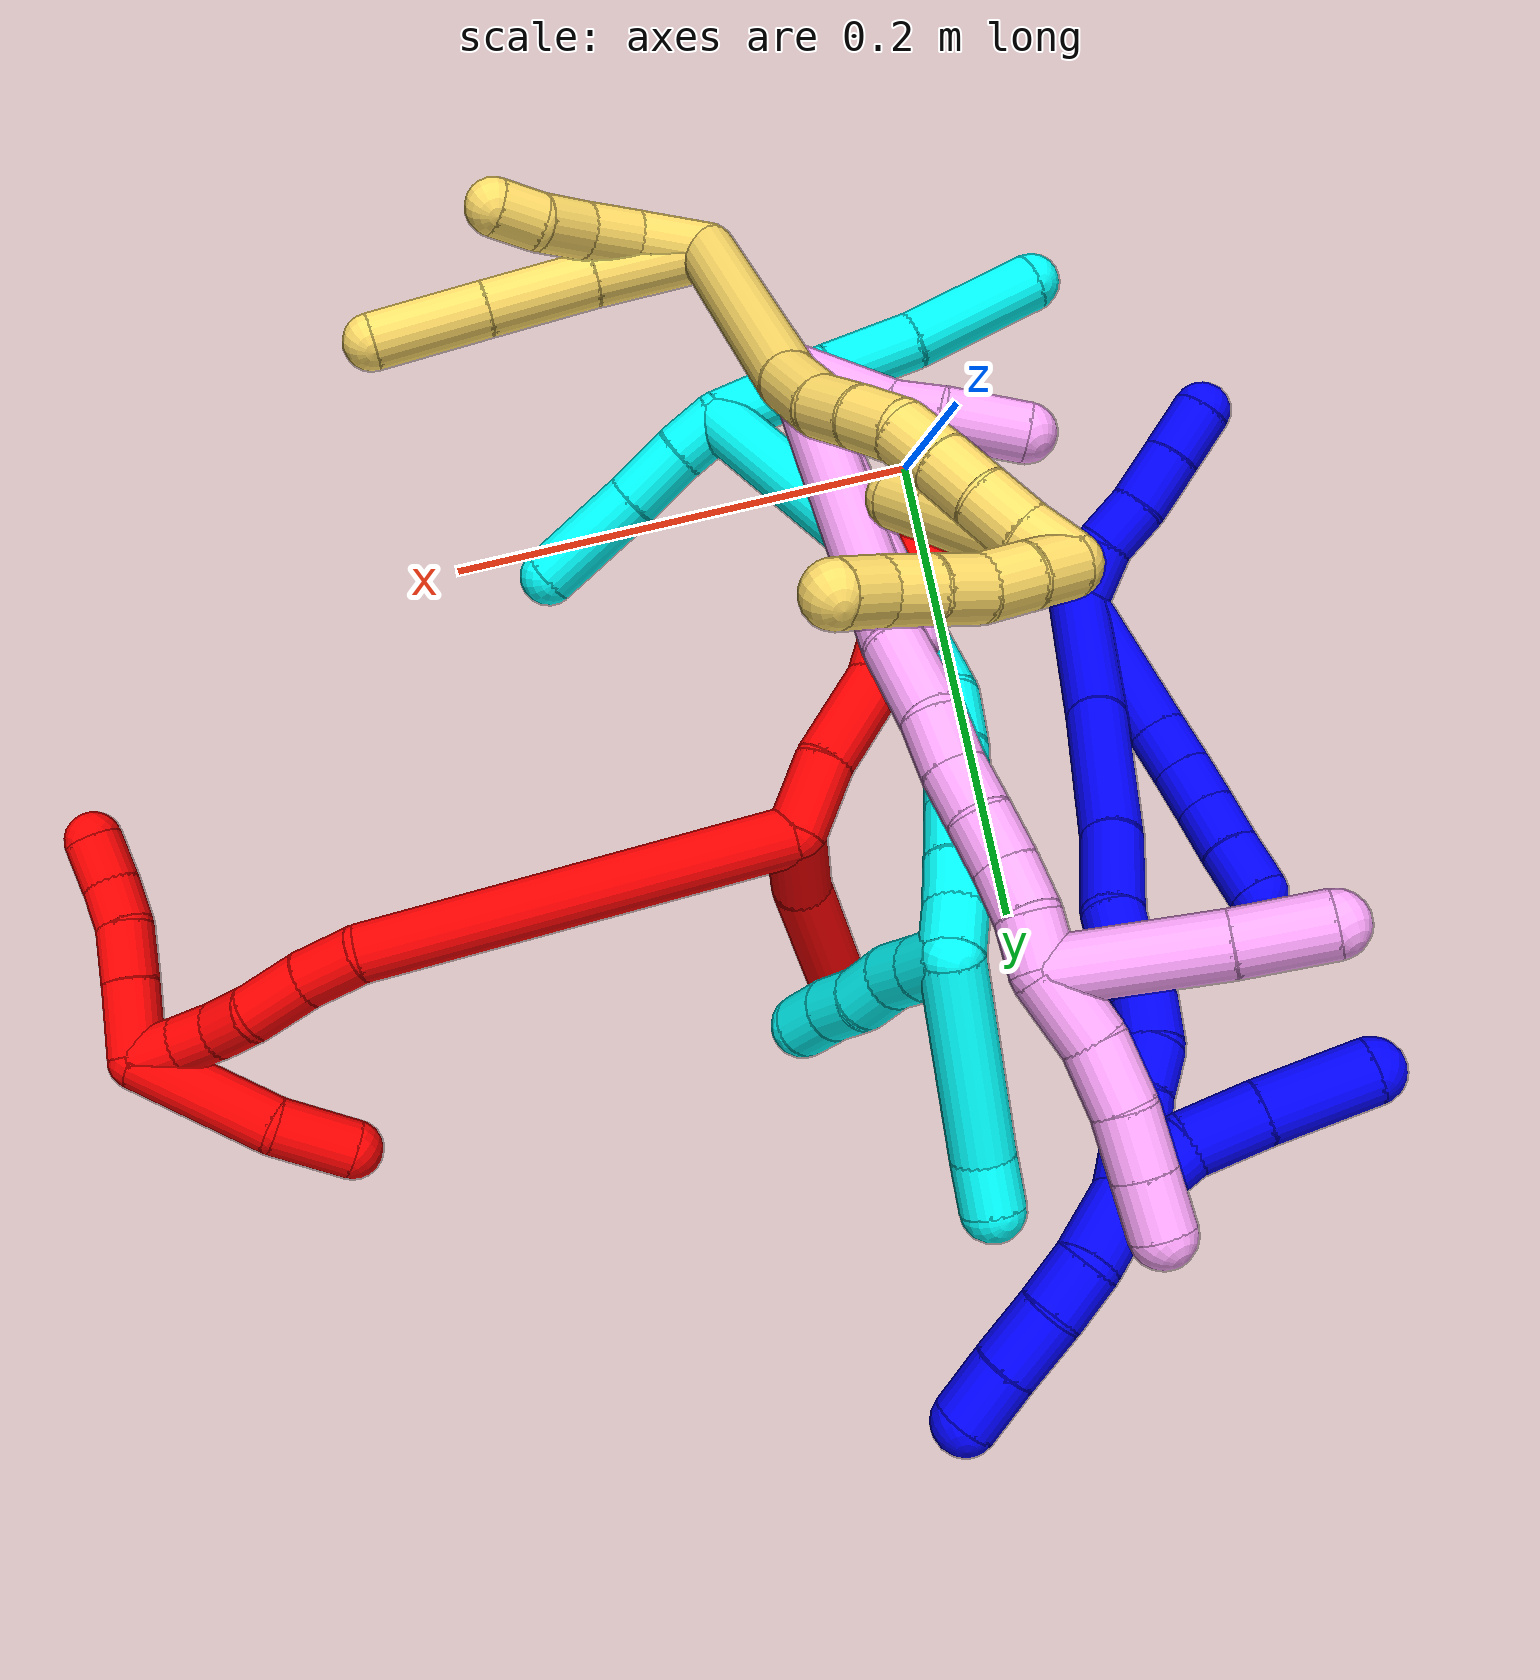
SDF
<sdf version="1.7">
 <world name="default">
  <plugin name="TubeGeneratorPlugin" filename="libtube_generator_plugin.so"/>
  <model name="photoneo_s_sensor">
   <static>1</static>
   <pose>0 0 2 1.57079 1.57079 3.14159</pose>
   <link name="link">
    <inertial><mass>0.1</mass></inertial>
    <sensor name="sensor" type="depth">
     <update_rate>30</update_rate>
     <camera>
      <horizontal_fov>1.22</horizontal_fov>
      <image><width>1920</width><height>1200</height><format>B8G8R8</format></image>
      <clip><near>0.1</near><far>4</far></clip>
      <depth_camera><output>points</output></depth_camera>
     </camera>
     <plugin name="camera_plugin" filename="libgazebo_ros_depth_camera.so">
      <baseline>0.2</baseline>
      <alwaysOn>1</alwaysOn>
      <updateRate>0.0</updateRate>
      <cameraName>camera_ir</cameraName>
      <imageTopicName>/camera/color/image_raw</imageTopicName>
      <cameraInfoTopicName>/camera/color/camera_info</cameraInfoTopicName>
      <depthImageTopicName>/camera/depth/image_raw</depthImageTopicName>
      <depthImageCameraInfoTopicName>/camera/depth/camera_info</depthImageCameraInfoTopicName>
      <pointCloudTopicName>/camera/depth/points</pointCloudTopicName>
      <frameName>fr_optical</frameName>
      <pointCloudCutoff>0.1</pointCloudCutoff>
      <pointCloudCutoffMax>2.0</pointCloudCutoffMax>
      <distortionK1>0</distortionK1>
      <distortionK2>0</distortionK2>
      <distortionK3>0</distortionK3>
      <distortionT1>0</distortionT1>
      <distortionT2>0</distortionT2>
      <CxPrime>0</CxPrime>
      <Cx>0</Cx>
      <Cy>0</Cy>
      <focalLength>0</focalLength>
      <hackBaseline>0</hackBaseline>
     </plugin>
    </sensor>
   </link>
  </model>
  <gravity>0 0 -9.8</gravity>
  <magnetic_field>6e-06 2.3e-05 -4.2e-05</magnetic_field>
  <atmosphere type="adiabatic"/>
  <physics name="default_physics" default="0" type="ode">
   <max_step_size>0.003</max_step_size>
   <real_time_factor>1</real_time_factor>
   <real_time_update_rate>1000</real_time_update_rate>
   <max_contacts>10000</max_contacts>
   <ode>
    <solver>
     <type>quick</type>
     <iters>100</iters>
     <sor>1.3</sor>
     <use_dynamic_moi_rescaling>0</use_dynamic_moi_rescaling>
    </solver>
    <constraints>
     <contact_max_correcting_vel>0</contact_max_correcting_vel>
     <contact_surface_layer>0.001</contact_surface_layer>
     <cfm>0</cfm>
     <erp>0.2</erp>
    </constraints>
   </ode>
  </physics>
  <scene><ambient>0.4 0.4 0.4 1</ambient><background>0.7 0.7 0.7 1</background><shadows>0</shadows></scene>
  <audio><device>default</device></audio>
  <spherical_coordinates>
   <surface_model>EARTH_WGS84</surface_model>
   <latitude_deg>0</latitude_deg>
   <longitude_deg>0</longitude_deg>
   <elevation>0</elevation>
   <heading_deg>0</heading_deg>
  </spherical_coordinates>
  <model name="bin">
   <static>1</static>
   <link name="bottom">
    <collision name="collision-bottom">
     <pose>0 0 -0.01 0 -0 0</pose>
     <geometry><box><size>0.8 0.6 0.02</size></box></geometry>
     <surface>
      <friction><ode><mu>100</mu><mu2>100</mu2></ode></friction>
      <contact><collide_bitmask>65535</collide_bitmask></contact>
     </surface>
    </collision>
   </link>
   <link name="west_wall">
    <collision name="collision-west_wall">
     <pose>-0.41 0 0.1 0 -0 0</pose>
     <geometry><box><size>0.02 0.6 0.2</size></box></geometry>
     <surface>
      <friction><ode><mu>100</mu><mu2>100</mu2></ode></friction>
      <contact><collide_bitmask>65535</collide_bitmask></contact>
     </surface>
    </collision>
   </link>
   <link name="east_wall">
    <collision name="collision-east_wall">
     <pose>0.41 0 0.1 0 -0 0</pose>
     <geometry><box><size>0.02 0.6 0.2</size></box></geometry>
     <surface>
      <friction><ode><mu>100</mu><mu2>100</mu2></ode></friction>
      <contact><collide_bitmask>65535</collide_bitmask></contact>
     </surface>
    </collision>
   </link>
   <link name="south_wall">
    <collision name="collision-south_wall">
     <pose>0 -0.31 0.1 0 -0 0</pose>
     <geometry><box><size>0.8 0.02 0.2</size></box></geometry>
     <surface>
      <friction><ode><mu>100</mu><mu2>100</mu2></ode></friction>
      <contact><collide_bitmask>65535</collide_bitmask></contact>
     </surface>
    </collision>
   </link>
   <link name="north_wall">
    <collision name="collision-north_wall">
     <pose>0 0.31 0.1 0 -0 0</pose>
     <geometry><box><size>0.8 0.02 0.2</size></box></geometry>
     <surface>
      <friction><ode><mu>100</mu><mu2>100</mu2></ode></friction>
      <contact><collide_bitmask>65535</collide_bitmask></contact>
     </surface>
    </collision>
   </link>
  </model>
  <model name="1">
   <static>0</static>
   <link name="1">
    <collision name="collision-cylinder-e_1_2_8">
     <pose>-0.018142 0.006258 0.026969 -0.228025 -0.580071 0.068324</pose>
     <geometry><cylinder><radius>0.0125</radius><length>0.0662</length></cylinder></geometry>
     <surface>
      <friction><ode><mu>1.16</mu><mu2>1.16</mu2><slip1>0</slip1><slip2>0</slip2></ode></friction>
      <contact><ode><kp>1e+06</kp><kd>1</kd><max_vel>0</max_vel><min_depth>0.001</min_depth></ode></contact>
     </surface>
    </collision>
    <visual name="visual-cylinder-e_1_2_8">
     <pose>-0.018142 0.006258 0.026969 -0.228025 -0.580071 0.068324</pose>
     <geometry><cylinder><radius>0.0125</radius><length>0.0662</length></cylinder></geometry>
     <material><ambient>0 0 1 1</ambient></material>
    </visual>
    <collision name="collision-cylinder-e_2_8_9">
     <pose>-0.041552 0.013997 0.062489 -0.171379 -0.545657 0.048061</pose>
     <geometry><cylinder><radius>0.0125</radius><length>0.020306</length></cylinder></geometry>
     <surface>
      <friction><ode><mu>1.16</mu><mu2>1.16</mu2><slip1>0</slip1><slip2>0</slip2></ode></friction>
      <contact><ode><kp>1e+06</kp><kd>1</kd><max_vel>0</max_vel><min_depth>0.001</min_depth></ode></contact>
     </surface>
    </collision>
    <visual name="visual-cylinder-e_2_8_9">
     <pose>-0.041552 0.013997 0.062489 -0.171379 -0.545657 0.048061</pose>
     <geometry><cylinder><radius>0.0125</radius><length>0.020306</length></cylinder></geometry>
     <material><ambient>0 0 1 1</ambient></material>
    </visual>
    <collision name="collision-cylinder-e_3_9_10">
     <pose>-0.051677 0.01679 0.079745 -0.14973 -0.504053 0.038623</pose>
     <geometry><cylinder><radius>0.0125</radius><length>0.020106</length></cylinder></geometry>
     <surface>
      <friction><ode><mu>1.16</mu><mu2>1.16</mu2><slip1>0</slip1><slip2>0</slip2></ode></friction>
      <contact><ode><kp>1e+06</kp><kd>1</kd><max_vel>0</max_vel><min_depth>0.001</min_depth></ode></contact>
     </surface>
    </collision>
    <visual name="visual-cylinder-e_3_9_10">
     <pose>-0.051677 0.01679 0.079745 -0.14973 -0.504053 0.038623</pose>
     <geometry><cylinder><radius>0.0125</radius><length>0.020106</length></cylinder></geometry>
     <material><ambient>0 0 1 1</ambient></material>
    </visual>
    <collision name="collision-cylinder-e_4_10_11">
     <pose>-0.060984 0.019035 0.097905 -0.098196 -0.438135 0.021879</pose>
     <geometry><cylinder><radius>0.0125</radius><length>0.020985</length></cylinder></geometry>
     <surface>
      <friction><ode><mu>1.16</mu><mu2>1.16</mu2><slip1>0</slip1><slip2>0</slip2></ode></friction>
      <contact><ode><kp>1e+06</kp><kd>1</kd><max_vel>0</max_vel><min_depth>0.001</min_depth></ode></contact>
     </surface>
    </collision>
    <visual name="visual-cylinder-e_4_10_11">
     <pose>-0.060984 0.019035 0.097905 -0.098196 -0.438135 0.021879</pose>
     <geometry><cylinder><radius>0.0125</radius><length>0.020985</length></cylinder></geometry>
     <material><ambient>0 0 1 1</ambient></material>
    </visual>
    <collision name="collision-cylinder-e_5_11_6">
     <pose>-0.070785 0.020998 0.117148 -0.10502 -0.497927 0.026723</pose>
     <geometry><cylinder><radius>0.0125</radius><length>0.022403</length></cylinder></geometry>
     <surface>
      <friction><ode><mu>1.16</mu><mu2>1.16</mu2><slip1>0</slip1><slip2>0</slip2></ode></friction>
      <contact><ode><kp>1e+06</kp><kd>1</kd><max_vel>0</max_vel><min_depth>0.001</min_depth></ode></contact>
     </surface>
    </collision>
    <visual name="visual-cylinder-e_5_11_6">
     <pose>-0.070785 0.020998 0.117148 -0.10502 -0.497927 0.026723</pose>
     <geometry><cylinder><radius>0.0125</radius><length>0.022403</length></cylinder></geometry>
     <material><ambient>0 0 1 1</ambient></material>
    </visual>
    <collision name="collision-cylinder-e_1_2_12">
     <pose>-0.00156 -0.011194 -0.007921 2.18661 -0.113242 -0.218222</pose>
     <geometry><cylinder><radius>0.0125</radius><length>0.027604</length></cylinder></geometry>
     <surface>
      <friction><ode><mu>1.16</mu><mu2>1.16</mu2><slip1>0</slip1><slip2>0</slip2></ode></friction>
      <contact><ode><kp>1e+06</kp><kd>1</kd><max_vel>0</max_vel><min_depth>0.001</min_depth></ode></contact>
     </surface>
    </collision>
    <visual name="visual-cylinder-e_1_2_12">
     <pose>-0.00156 -0.011194 -0.007921 2.18661 -0.113242 -0.218222</pose>
     <geometry><cylinder><radius>0.0125</radius><length>0.027604</length></cylinder></geometry>
     <material><ambient>0 0 1 1</ambient></material>
    </visual>
    <collision name="collision-cylinder-e_2_12_13">
     <pose>-0.007916 -0.030567 -0.021464 2.17294 -0.450243 -0.821072</pose>
     <geometry><cylinder><radius>0.0125</radius><length>0.022045</length></cylinder></geometry>
     <surface>
      <friction><ode><mu>1.16</mu><mu2>1.16</mu2><slip1>0</slip1><slip2>0</slip2></ode></friction>
      <contact><ode><kp>1e+06</kp><kd>1</kd><max_vel>0</max_vel><min_depth>0.001</min_depth></ode></contact>
     </surface>
    </collision>
    <visual name="visual-cylinder-e_2_12_13">
     <pose>-0.007916 -0.030567 -0.021464 2.17294 -0.450243 -0.821072</pose>
     <geometry><cylinder><radius>0.0125</radius><length>0.022045</length></cylinder></geometry>
     <material><ambient>0 0 1 1</ambient></material>
    </visual>
    <collision name="collision-cylinder-e_3_13_14">
     <pose>-0.01693 -0.048303 -0.034982 2.26137 -0.327861 -0.675594</pose>
     <geometry><cylinder><radius>0.0125</radius><length>0.02619</length></cylinder></geometry>
     <surface>
      <friction><ode><mu>1.16</mu><mu2>1.16</mu2><slip1>0</slip1><slip2>0</slip2></ode></friction>
      <contact><ode><kp>1e+06</kp><kd>1</kd><max_vel>0</max_vel><min_depth>0.001</min_depth></ode></contact>
     </surface>
    </collision>
    <visual name="visual-cylinder-e_3_13_14">
     <pose>-0.01693 -0.048303 -0.034982 2.26137 -0.327861 -0.675594</pose>
     <geometry><cylinder><radius>0.0125</radius><length>0.02619</length></cylinder></geometry>
     <material><ambient>0 0 1 1</ambient></material>
    </visual>
    <collision name="collision-cylinder-e_4_14_5">
     <pose>-0.025086 -0.066499 -0.050347 2.28365 -0.332165 -0.702585</pose>
     <geometry><cylinder><radius>0.0125</radius><length>0.024161</length></cylinder></geometry>
     <surface>
      <friction><ode><mu>1.16</mu><mu2>1.16</mu2><slip1>0</slip1><slip2>0</slip2></ode></friction>
      <contact><ode><kp>1e+06</kp><kd>1</kd><max_vel>0</max_vel><min_depth>0.001</min_depth></ode></contact>
     </surface>
    </collision>
    <visual name="visual-cylinder-e_4_14_5">
     <pose>-0.025086 -0.066499 -0.050347 2.28365 -0.332165 -0.702585</pose>
     <geometry><cylinder><radius>0.0125</radius><length>0.024161</length></cylinder></geometry>
     <material><ambient>0 0 1 1</ambient></material>
    </visual>
    <collision name="collision-cylinder-e_1_2_15">
     <pose>0.000826 -0.000609 0.037196 0.016366 0.022189 0.000182</pose>
     <geometry><cylinder><radius>0.0125</radius><length>0.074421</length></cylinder></geometry>
     <surface>
      <friction><ode><mu>1.16</mu><mu2>1.16</mu2><slip1>0</slip1><slip2>0</slip2></ode></friction>
      <contact><ode><kp>1e+06</kp><kd>1</kd><max_vel>0</max_vel><min_depth>0.001</min_depth></ode></contact>
     </surface>
    </collision>
    <visual name="visual-cylinder-e_1_2_15">
     <pose>0.000826 -0.000609 0.037196 0.016366 0.022189 0.000182</pose>
     <geometry><cylinder><radius>0.0125</radius><length>0.074421</length></cylinder></geometry>
     <material><ambient>0 0 1 1</ambient></material>
    </visual>
    <collision name="collision-cylinder-e_2_15_16">
     <pose>0.002172 0.000132 0.108194 -0.039903 0.015393 -0.000307</pose>
     <geometry><cylinder><radius>0.0125</radius><length>0.067665</length></cylinder></geometry>
     <surface>
      <friction><ode><mu>1.16</mu><mu2>1.16</mu2><slip1>0</slip1><slip2>0</slip2></ode></friction>
      <contact><ode><kp>1e+06</kp><kd>1</kd><max_vel>0</max_vel><min_depth>0.001</min_depth></ode></contact>
     </surface>
    </collision>
    <visual name="visual-cylinder-e_2_15_16">
     <pose>0.002172 0.000132 0.108194 -0.039903 0.015393 -0.000307</pose>
     <geometry><cylinder><radius>0.0125</radius><length>0.067665</length></cylinder></geometry>
     <material><ambient>0 0 1 1</ambient></material>
    </visual>
    <collision name="collision-cylinder-e_3_16_17">
     <pose>0.003862 0.003722 0.160255 -0.122072 0.063483 -0.003881</pose>
     <geometry><cylinder><radius>0.0125</radius><length>0.036868</length></cylinder></geometry>
     <surface>
      <friction><ode><mu>1.16</mu><mu2>1.16</mu2><slip1>0</slip1><slip2>0</slip2></ode></friction>
      <contact><ode><kp>1e+06</kp><kd>1</kd><max_vel>0</max_vel><min_depth>0.001</min_depth></ode></contact>
     </surface>
    </collision>
    <visual name="visual-cylinder-e_3_16_17">
     <pose>0.003862 0.003722 0.160255 -0.122072 0.063483 -0.003881</pose>
     <geometry><cylinder><radius>0.0125</radius><length>0.036868</length></cylinder></geometry>
     <material><ambient>0 0 1 1</ambient></material>
    </visual>
    <collision name="collision-cylinder-e_4_17_18">
     <pose>0.003189 0.00738 0.188351 -0.143176 -0.183322 0.013183</pose>
     <geometry><cylinder><radius>0.0125</radius><length>0.020213</length></cylinder></geometry>
     <surface>
      <friction><ode><mu>1.16</mu><mu2>1.16</mu2><slip1>0</slip1><slip2>0</slip2></ode></friction>
      <contact><ode><kp>1e+06</kp><kd>1</kd><max_vel>0</max_vel><min_depth>0.001</min_depth></ode></contact>
     </surface>
    </collision>
    <visual name="visual-cylinder-e_4_17_18">
     <pose>0.003189 0.00738 0.188351 -0.143176 -0.183322 0.013183</pose>
     <geometry><cylinder><radius>0.0125</radius><length>0.020213</length></cylinder></geometry>
     <material><ambient>0 0 1 1</ambient></material>
    </visual>
    <collision name="collision-cylinder-e_5_18_19">
     <pose>-0.001168 0.008535 0.208077 0.026537 -0.24891 -0.00332</pose>
     <geometry><cylinder><radius>0.0125</radius><length>0.020419</length></cylinder></geometry>
     <surface>
      <friction><ode><mu>1.16</mu><mu2>1.16</mu2><slip1>0</slip1><slip2>0</slip2></ode></friction>
      <contact><ode><kp>1e+06</kp><kd>1</kd><max_vel>0</max_vel><min_depth>0.001</min_depth></ode></contact>
     </surface>
    </collision>
    <visual name="visual-cylinder-e_5_18_19">
     <pose>-0.001168 0.008535 0.208077 0.026537 -0.24891 -0.00332</pose>
     <geometry><cylinder><radius>0.0125</radius><length>0.020419</length></cylinder></geometry>
     <material><ambient>0 0 1 1</ambient></material>
    </visual>
    <collision name="collision-cylinder-e_6_19_20">
     <pose>-0.004482 0.00976 0.227987 -0.147457 -0.078727 0.005818</pose>
     <geometry><cylinder><radius>0.0125</radius><length>0.02032</length></cylinder></geometry>
     <surface>
      <friction><ode><mu>1.16</mu><mu2>1.16</mu2><slip1>0</slip1><slip2>0</slip2></ode></friction>
      <contact><ode><kp>1e+06</kp><kd>1</kd><max_vel>0</max_vel><min_depth>0.001</min_depth></ode></contact>
     </surface>
    </collision>
    <visual name="visual-cylinder-e_6_19_20">
     <pose>-0.004482 0.00976 0.227987 -0.147457 -0.078727 0.005818</pose>
     <geometry><cylinder><radius>0.0125</radius><length>0.02032</length></cylinder></geometry>
     <material><ambient>0 0 1 1</ambient></material>
    </visual>
    <collision name="collision-cylinder-e_7_20_21">
     <pose>-0.003102 0.014414 0.247269 -0.329263 0.219065 -0.036537</pose>
     <geometry><cylinder><radius>0.0125</radius><length>0.020059</length></cylinder></geometry>
     <surface>
      <friction><ode><mu>1.16</mu><mu2>1.16</mu2><slip1>0</slip1><slip2>0</slip2></ode></friction>
      <contact><ode><kp>1e+06</kp><kd>1</kd><max_vel>0</max_vel><min_depth>0.001</min_depth></ode></contact>
     </surface>
    </collision>
    <visual name="visual-cylinder-e_7_20_21">
     <pose>-0.003102 0.014414 0.247269 -0.329263 0.219065 -0.036537</pose>
     <geometry><cylinder><radius>0.0125</radius><length>0.020059</length></cylinder></geometry>
     <material><ambient>0 0 1 1</ambient></material>
    </visual>
    <collision name="collision-cylinder-e_8_21_22">
     <pose>-0.000806 0.021914 0.265561 -0.447644 0.011615 -0.002644</pose>
     <geometry><cylinder><radius>0.0125</radius><length>0.020029</length></cylinder></geometry>
     <surface>
      <friction><ode><mu>1.16</mu><mu2>1.16</mu2><slip1>0</slip1><slip2>0</slip2></ode></friction>
      <contact><ode><kp>1e+06</kp><kd>1</kd><max_vel>0</max_vel><min_depth>0.001</min_depth></ode></contact>
     </surface>
    </collision>
    <visual name="visual-cylinder-e_8_21_22">
     <pose>-0.000806 0.021914 0.265561 -0.447644 0.011615 -0.002644</pose>
     <geometry><cylinder><radius>0.0125</radius><length>0.020029</length></cylinder></geometry>
     <material><ambient>0 0 1 1</ambient></material>
    </visual>
    <collision name="collision-cylinder-e_9_22_1">
     <pose>0.001317 0.028485 0.284129 -0.230239 0.201949 -0.02343</pose>
     <geometry><cylinder><radius>0.0125</radius><length>0.020007</length></cylinder></geometry>
     <surface>
      <friction><ode><mu>1.16</mu><mu2>1.16</mu2><slip1>0</slip1><slip2>0</slip2></ode></friction>
      <contact><ode><kp>1e+06</kp><kd>1</kd><max_vel>0</max_vel><min_depth>0.001</min_depth></ode></contact>
     </surface>
    </collision>
    <visual name="visual-cylinder-e_9_22_1">
     <pose>0.001317 0.028485 0.284129 -0.230239 0.201949 -0.02343</pose>
     <geometry><cylinder><radius>0.0125</radius><length>0.020007</length></cylinder></geometry>
     <material><ambient>0 0 1 1</ambient></material>
    </visual>
    <collision name="collision-cylinder-e_1_1_23">
     <pose>-0.005497 0.022224 0.286135 2.2963 -0.660336 -1.30229</pose>
     <geometry><cylinder><radius>0.0125</radius><length>0.02876</length></cylinder></geometry>
     <surface>
      <friction><ode><mu>1.16</mu><mu2>1.16</mu2><slip1>0</slip1><slip2>0</slip2></ode></friction>
      <contact><ode><kp>1e+06</kp><kd>1</kd><max_vel>0</max_vel><min_depth>0.001</min_depth></ode></contact>
     </surface>
    </collision>
    <visual name="visual-cylinder-e_1_1_23">
     <pose>-0.005497 0.022224 0.286135 2.2963 -0.660336 -1.30229</pose>
     <geometry><cylinder><radius>0.0125</radius><length>0.02876</length></cylinder></geometry>
     <material><ambient>0 0 1 1</ambient></material>
    </visual>
    <collision name="collision-cylinder-e_2_23_24">
     <pose>-0.025481 0.005282 0.274555 2.0175 -0.872844 -1.27488</pose>
     <geometry><cylinder><radius>0.0125</radius><length>0.029141</length></cylinder></geometry>
     <surface>
      <friction><ode><mu>1.16</mu><mu2>1.16</mu2><slip1>0</slip1><slip2>0</slip2></ode></friction>
      <contact><ode><kp>1e+06</kp><kd>1</kd><max_vel>0</max_vel><min_depth>0.001</min_depth></ode></contact>
     </surface>
    </collision>
    <visual name="visual-cylinder-e_2_23_24">
     <pose>-0.025481 0.005282 0.274555 2.0175 -0.872844 -1.27488</pose>
     <geometry><cylinder><radius>0.0125</radius><length>0.029141</length></cylinder></geometry>
     <material><ambient>0 0 1 1</ambient></material>
    </visual>
    <collision name="collision-cylinder-e_3_24_4">
     <pose>-0.053212 -0.015073 0.265338 1.98043 -0.906057 -1.27681</pose>
     <geometry><cylinder><radius>0.0125</radius><length>0.042099</length></cylinder></geometry>
     <surface>
      <friction><ode><mu>1.16</mu><mu2>1.16</mu2><slip1>0</slip1><slip2>0</slip2></ode></friction>
      <contact><ode><kp>1e+06</kp><kd>1</kd><max_vel>0</max_vel><min_depth>0.001</min_depth></ode></contact>
     </surface>
    </collision>
    <visual name="visual-cylinder-e_3_24_4">
     <pose>-0.053212 -0.015073 0.265338 1.98043 -0.906057 -1.27681</pose>
     <geometry><cylinder><radius>0.0125</radius><length>0.042099</length></cylinder></geometry>
     <material><ambient>0 0 1 1</ambient></material>
    </visual>
    <collision name="collision-cylinder-e_1_1_25">
     <pose>0.009212 0.037133 0.305179 -0.508322 0.420344 -0.11072</pose>
     <geometry><cylinder><radius>0.0125</radius><length>0.028858</length></cylinder></geometry>
     <surface>
      <friction><ode><mu>1.16</mu><mu2>1.16</mu2><slip1>0</slip1><slip2>0</slip2></ode></friction>
      <contact><ode><kp>1e+06</kp><kd>1</kd><max_vel>0</max_vel><min_depth>0.001</min_depth></ode></contact>
     </surface>
    </collision>
    <visual name="visual-cylinder-e_1_1_25">
     <pose>0.009212 0.037133 0.305179 -0.508322 0.420344 -0.11072</pose>
     <geometry><cylinder><radius>0.0125</radius><length>0.028858</length></cylinder></geometry>
     <material><ambient>0 0 1 1</ambient></material>
    </visual>
    <collision name="collision-cylinder-e_2_25_26">
     <pose>0.01921 0.051167 0.322945 -0.883254 0.394838 -0.18857</pose>
     <geometry><cylinder><radius>0.0125</radius><length>0.02137</length></cylinder></geometry>
     <surface>
      <friction><ode><mu>1.16</mu><mu2>1.16</mu2><slip1>0</slip1><slip2>0</slip2></ode></friction>
      <contact><ode><kp>1e+06</kp><kd>1</kd><max_vel>0</max_vel><min_depth>0.001</min_depth></ode></contact>
     </surface>
    </collision>
    <visual name="visual-cylinder-e_2_25_26">
     <pose>0.01921 0.051167 0.322945 -0.883254 0.394838 -0.18857</pose>
     <geometry><cylinder><radius>0.0125</radius><length>0.02137</length></cylinder></geometry>
     <material><ambient>0 0 1 1</ambient></material>
    </visual>
    <collision name="collision-cylinder-e_3_26_27">
     <pose>0.027848 0.069025 0.335266 -1.03616 0.363694 -0.208864</pose>
     <geometry><cylinder><radius>0.0125</radius><length>0.025457</length></cylinder></geometry>
     <surface>
      <friction><ode><mu>1.16</mu><mu2>1.16</mu2><slip1>0</slip1><slip2>0</slip2></ode></friction>
      <contact><ode><kp>1e+06</kp><kd>1</kd><max_vel>0</max_vel><min_depth>0.001</min_depth></ode></contact>
     </surface>
    </collision>
    <visual name="visual-cylinder-e_3_26_27">
     <pose>0.027848 0.069025 0.335266 -1.03616 0.363694 -0.208864</pose>
     <geometry><cylinder><radius>0.0125</radius><length>0.025457</length></cylinder></geometry>
     <material><ambient>0 0 1 1</ambient></material>
    </visual>
    <collision name="collision-cylinder-e_4_27_3">
     <pose>0.03612 0.089344 0.346994 -1.05883 0.313077 -0.184181</pose>
     <geometry><cylinder><radius>0.0125</radius><length>0.024315</length></cylinder></geometry>
     <surface>
      <friction><ode><mu>1.16</mu><mu2>1.16</mu2><slip1>0</slip1><slip2>0</slip2></ode></friction>
      <contact><ode><kp>1e+06</kp><kd>1</kd><max_vel>0</max_vel><min_depth>0.001</min_depth></ode></contact>
     </surface>
    </collision>
    <visual name="visual-cylinder-e_4_27_3">
     <pose>0.03612 0.089344 0.346994 -1.05883 0.313077 -0.184181</pose>
     <geometry><cylinder><radius>0.0125</radius><length>0.024315</length></cylinder></geometry>
     <material><ambient>0 0 1 1</ambient></material>
    </visual>
    <collision name="collision-sphere-3">
     <pose>0.039864 0.099427 0.35266 0 -0 0</pose>
     <geometry><sphere><radius>0.0125</radius></sphere></geometry>
     <surface>
      <friction><ode><mu>1.16</mu><mu2>1.16</mu2><slip1>0</slip1><slip2>0</slip2></ode></friction>
      <contact><ode><kp>1e+06</kp><kd>1</kd><max_vel>0</max_vel><min_depth>0.001</min_depth></ode></contact>
     </surface>
    </collision>
    <visual name="visual-sphere-3">
     <pose>0.039864 0.099427 0.35266 0 -0 0</pose>
     <geometry><sphere><radius>0.0125</radius></sphere></geometry>
     <material><ambient>0 0 1 1</ambient></material>
    </visual>
    <collision name="collision-sphere-27">
     <pose>0.032376 0.07926 0.341327 0 -0 0</pose>
     <geometry><sphere><radius>0.0125</radius></sphere></geometry>
     <surface>
      <friction><ode><mu>1.16</mu><mu2>1.16</mu2><slip1>0</slip1><slip2>0</slip2></ode></friction>
      <contact><ode><kp>1e+06</kp><kd>1</kd><max_vel>0</max_vel><min_depth>0.001</min_depth></ode></contact>
     </surface>
    </collision>
    <visual name="visual-sphere-27">
     <pose>0.032376 0.07926 0.341327 0 -0 0</pose>
     <geometry><sphere><radius>0.0125</radius></sphere></geometry>
     <material><ambient>0 0 1 1</ambient></material>
    </visual>
    <collision name="collision-sphere-26">
     <pose>0.02332 0.058789 0.329205 0 -0 0</pose>
     <geometry><sphere><radius>0.0125</radius></sphere></geometry>
     <surface>
      <friction><ode><mu>1.16</mu><mu2>1.16</mu2><slip1>0</slip1><slip2>0</slip2></ode></friction>
      <contact><ode><kp>1e+06</kp><kd>1</kd><max_vel>0</max_vel><min_depth>0.001</min_depth></ode></contact>
     </surface>
    </collision>
    <visual name="visual-sphere-26">
     <pose>0.02332 0.058789 0.329205 0 -0 0</pose>
     <geometry><sphere><radius>0.0125</radius></sphere></geometry>
     <material><ambient>0 0 1 1</ambient></material>
    </visual>
    <collision name="collision-sphere-25">
     <pose>0.0151 0.043544 0.316686 0 -0 0</pose>
     <geometry><sphere><radius>0.0125</radius></sphere></geometry>
     <surface>
      <friction><ode><mu>1.16</mu><mu2>1.16</mu2><slip1>0</slip1><slip2>0</slip2></ode></friction>
      <contact><ode><kp>1e+06</kp><kd>1</kd><max_vel>0</max_vel><min_depth>0.001</min_depth></ode></contact>
     </surface>
    </collision>
    <visual name="visual-sphere-25">
     <pose>0.0151 0.043544 0.316686 0 -0 0</pose>
     <geometry><sphere><radius>0.0125</radius></sphere></geometry>
     <material><ambient>0 0 1 1</ambient></material>
    </visual>
    <collision name="collision-sphere-4">
     <pose>-0.069779 -0.026983 0.260167 0 -0 0</pose>
     <geometry><sphere><radius>0.0125</radius></sphere></geometry>
     <surface>
      <friction><ode><mu>1.16</mu><mu2>1.16</mu2><slip1>0</slip1><slip2>0</slip2></ode></friction>
      <contact><ode><kp>1e+06</kp><kd>1</kd><max_vel>0</max_vel><min_depth>0.001</min_depth></ode></contact>
     </surface>
    </collision>
    <visual name="visual-sphere-4">
     <pose>-0.069779 -0.026983 0.260167 0 -0 0</pose>
     <geometry><sphere><radius>0.0125</radius></sphere></geometry>
     <material><ambient>0 0 1 1</ambient></material>
    </visual>
    <collision name="collision-sphere-24">
     <pose>-0.036644 -0.003162 0.270509 0 -0 0</pose>
     <geometry><sphere><radius>0.0125</radius></sphere></geometry>
     <surface>
      <friction><ode><mu>1.16</mu><mu2>1.16</mu2><slip1>0</slip1><slip2>0</slip2></ode></friction>
      <contact><ode><kp>1e+06</kp><kd>1</kd><max_vel>0</max_vel><min_depth>0.001</min_depth></ode></contact>
     </surface>
    </collision>
    <visual name="visual-sphere-24">
     <pose>-0.036644 -0.003162 0.270509 0 -0 0</pose>
     <geometry><sphere><radius>0.0125</radius></sphere></geometry>
     <material><ambient>0 0 1 1</ambient></material>
    </visual>
    <collision name="collision-sphere-23">
     <pose>-0.014317 0.013727 0.2786 0 -0 0</pose>
     <geometry><sphere><radius>0.0125</radius></sphere></geometry>
     <surface>
      <friction><ode><mu>1.16</mu><mu2>1.16</mu2><slip1>0</slip1><slip2>0</slip2></ode></friction>
      <contact><ode><kp>1e+06</kp><kd>1</kd><max_vel>0</max_vel><min_depth>0.001</min_depth></ode></contact>
     </surface>
    </collision>
    <visual name="visual-sphere-23">
     <pose>-0.014317 0.013727 0.2786 0 -0 0</pose>
     <geometry><sphere><radius>0.0125</radius></sphere></geometry>
     <material><ambient>0 0 1 1</ambient></material>
    </visual>
    <collision name="collision-sphere-1">
     <pose>0.003324 0.030721 0.293671 0 -0 0</pose>
     <geometry><sphere><radius>0.0125</radius></sphere></geometry>
     <surface>
      <friction><ode><mu>1.16</mu><mu2>1.16</mu2><slip1>0</slip1><slip2>0</slip2></ode></friction>
      <contact><ode><kp>1e+06</kp><kd>1</kd><max_vel>0</max_vel><min_depth>0.001</min_depth></ode></contact>
     </surface>
    </collision>
    <visual name="visual-sphere-1">
     <pose>0.003324 0.030721 0.293671 0 -0 0</pose>
     <geometry><sphere><radius>0.0125</radius></sphere></geometry>
     <material><ambient>0 0 1 1</ambient></material>
    </visual>
    <collision name="collision-sphere-22">
     <pose>-0.000689 0.026248 0.274588 0 -0 0</pose>
     <geometry><sphere><radius>0.0125</radius></sphere></geometry>
     <surface>
      <friction><ode><mu>1.16</mu><mu2>1.16</mu2><slip1>0</slip1><slip2>0</slip2></ode></friction>
      <contact><ode><kp>1e+06</kp><kd>1</kd><max_vel>0</max_vel><min_depth>0.001</min_depth></ode></contact>
     </surface>
    </collision>
    <visual name="visual-sphere-22">
     <pose>-0.000689 0.026248 0.274588 0 -0 0</pose>
     <geometry><sphere><radius>0.0125</radius></sphere></geometry>
     <material><ambient>0 0 1 1</ambient></material>
    </visual>
    <collision name="collision-sphere-21">
     <pose>-0.000922 0.01758 0.256534 0 -0 0</pose>
     <geometry><sphere><radius>0.0125</radius></sphere></geometry>
     <surface>
      <friction><ode><mu>1.16</mu><mu2>1.16</mu2><slip1>0</slip1><slip2>0</slip2></ode></friction>
      <contact><ode><kp>1e+06</kp><kd>1</kd><max_vel>0</max_vel><min_depth>0.001</min_depth></ode></contact>
     </surface>
    </collision>
    <visual name="visual-sphere-21">
     <pose>-0.000922 0.01758 0.256534 0 -0 0</pose>
     <geometry><sphere><radius>0.0125</radius></sphere></geometry>
     <material><ambient>0 0 1 1</ambient></material>
    </visual>
    <collision name="collision-sphere-6">
     <pose>-0.076135 0.02203 0.126935 0 -0 0</pose>
     <geometry><sphere><radius>0.0125</radius></sphere></geometry>
     <surface>
      <friction><ode><mu>1.16</mu><mu2>1.16</mu2><slip1>0</slip1><slip2>0</slip2></ode></friction>
      <contact><ode><kp>1e+06</kp><kd>1</kd><max_vel>0</max_vel><min_depth>0.001</min_depth></ode></contact>
     </surface>
    </collision>
    <visual name="visual-sphere-6">
     <pose>-0.076135 0.02203 0.126935 0 -0 0</pose>
     <geometry><sphere><radius>0.0125</radius></sphere></geometry>
     <material><ambient>0 0 1 1</ambient></material>
    </visual>
    <collision name="collision-sphere-11">
     <pose>-0.065435 0.019966 0.107361 0 -0 0</pose>
     <geometry><sphere><radius>0.0125</radius></sphere></geometry>
     <surface>
      <friction><ode><mu>1.16</mu><mu2>1.16</mu2><slip1>0</slip1><slip2>0</slip2></ode></friction>
      <contact><ode><kp>1e+06</kp><kd>1</kd><max_vel>0</max_vel><min_depth>0.001</min_depth></ode></contact>
     </surface>
    </collision>
    <visual name="visual-sphere-11">
     <pose>-0.065435 0.019966 0.107361 0 -0 0</pose>
     <geometry><sphere><radius>0.0125</radius></sphere></geometry>
     <material><ambient>0 0 1 1</ambient></material>
    </visual>
    <collision name="collision-sphere-10">
     <pose>-0.056532 0.018103 0.088449 0 -0 0</pose>
     <geometry><sphere><radius>0.0125</radius></sphere></geometry>
     <surface>
      <friction><ode><mu>1.16</mu><mu2>1.16</mu2><slip1>0</slip1><slip2>0</slip2></ode></friction>
      <contact><ode><kp>1e+06</kp><kd>1</kd><max_vel>0</max_vel><min_depth>0.001</min_depth></ode></contact>
     </surface>
    </collision>
    <visual name="visual-sphere-10">
     <pose>-0.056532 0.018103 0.088449 0 -0 0</pose>
     <geometry><sphere><radius>0.0125</radius></sphere></geometry>
     <material><ambient>0 0 1 1</ambient></material>
    </visual>
    <collision name="collision-sphere-9">
     <pose>-0.046821 0.015477 0.07104 0 -0 0</pose>
     <geometry><sphere><radius>0.0125</radius></sphere></geometry>
     <surface>
      <friction><ode><mu>1.16</mu><mu2>1.16</mu2><slip1>0</slip1><slip2>0</slip2></ode></friction>
      <contact><ode><kp>1e+06</kp><kd>1</kd><max_vel>0</max_vel><min_depth>0.001</min_depth></ode></contact>
     </surface>
    </collision>
    <visual name="visual-sphere-9">
     <pose>-0.046821 0.015477 0.07104 0 -0 0</pose>
     <geometry><sphere><radius>0.0125</radius></sphere></geometry>
     <material><ambient>0 0 1 1</ambient></material>
    </visual>
    <collision name="collision-sphere-2">
     <geometry><sphere><radius>0.0125</radius></sphere></geometry>
     <surface>
      <friction><ode><mu>1.16</mu><mu2>1.16</mu2><slip1>0</slip1><slip2>0</slip2></ode></friction>
      <contact><ode><kp>1e+06</kp><kd>1</kd><max_vel>0</max_vel><min_depth>0.001</min_depth></ode></contact>
     </surface>
    </collision>
    <visual name="visual-sphere-2">
     <geometry><sphere><radius>0.0125</radius></sphere></geometry>
     <material><ambient>0 0 1 1</ambient></material>
    </visual>
    <collision name="collision-sphere-19">
     <pose>-0.003683 0.008272 0.217969 0 -0 0</pose>
     <geometry><sphere><radius>0.0125</radius></sphere></geometry>
     <surface>
      <friction><ode><mu>1.16</mu><mu2>1.16</mu2><slip1>0</slip1><slip2>0</slip2></ode></friction>
      <contact><ode><kp>1e+06</kp><kd>1</kd><max_vel>0</max_vel><min_depth>0.001</min_depth></ode></contact>
     </surface>
    </collision>
    <visual name="visual-sphere-19">
     <pose>-0.003683 0.008272 0.217969 0 -0 0</pose>
     <geometry><sphere><radius>0.0125</radius></sphere></geometry>
     <material><ambient>0 0 1 1</ambient></material>
    </visual>
    <collision name="collision-sphere-8">
     <pose>-0.036283 0.012517 0.053938 0 -0 0</pose>
     <geometry><sphere><radius>0.0125</radius></sphere></geometry>
     <surface>
      <friction><ode><mu>1.16</mu><mu2>1.16</mu2><slip1>0</slip1><slip2>0</slip2></ode></friction>
      <contact><ode><kp>1e+06</kp><kd>1</kd><max_vel>0</max_vel><min_depth>0.001</min_depth></ode></contact>
     </surface>
    </collision>
    <visual name="visual-sphere-8">
     <pose>-0.036283 0.012517 0.053938 0 -0 0</pose>
     <geometry><sphere><radius>0.0125</radius></sphere></geometry>
     <material><ambient>0 0 1 1</ambient></material>
    </visual>
    <collision name="collision-sphere-12">
     <pose>-0.003119 -0.022389 -0.015843 0 -0 0</pose>
     <geometry><sphere><radius>0.0125</radius></sphere></geometry>
     <surface>
      <friction><ode><mu>1.16</mu><mu2>1.16</mu2><slip1>0</slip1><slip2>0</slip2></ode></friction>
      <contact><ode><kp>1e+06</kp><kd>1</kd><max_vel>0</max_vel><min_depth>0.001</min_depth></ode></contact>
     </surface>
    </collision>
    <visual name="visual-sphere-12">
     <pose>-0.003119 -0.022389 -0.015843 0 -0 0</pose>
     <geometry><sphere><radius>0.0125</radius></sphere></geometry>
     <material><ambient>0 0 1 1</ambient></material>
    </visual>
    <collision name="collision-sphere-13">
     <pose>-0.012713 -0.038746 -0.027085 0 -0 0</pose>
     <geometry><sphere><radius>0.0125</radius></sphere></geometry>
     <surface>
      <friction><ode><mu>1.16</mu><mu2>1.16</mu2><slip1>0</slip1><slip2>0</slip2></ode></friction>
      <contact><ode><kp>1e+06</kp><kd>1</kd><max_vel>0</max_vel><min_depth>0.001</min_depth></ode></contact>
     </surface>
    </collision>
    <visual name="visual-sphere-13">
     <pose>-0.012713 -0.038746 -0.027085 0 -0 0</pose>
     <geometry><sphere><radius>0.0125</radius></sphere></geometry>
     <material><ambient>0 0 1 1</ambient></material>
    </visual>
    <collision name="collision-sphere-14">
     <pose>-0.021147 -0.05786 -0.042879 0 -0 0</pose>
     <geometry><sphere><radius>0.0125</radius></sphere></geometry>
     <surface>
      <friction><ode><mu>1.16</mu><mu2>1.16</mu2><slip1>0</slip1><slip2>0</slip2></ode></friction>
      <contact><ode><kp>1e+06</kp><kd>1</kd><max_vel>0</max_vel><min_depth>0.001</min_depth></ode></contact>
     </surface>
    </collision>
    <visual name="visual-sphere-14">
     <pose>-0.021147 -0.05786 -0.042879 0 -0 0</pose>
     <geometry><sphere><radius>0.0125</radius></sphere></geometry>
     <material><ambient>0 0 1 1</ambient></material>
    </visual>
    <collision name="collision-sphere-5">
     <pose>-0.029025 -0.075139 -0.057816 0 -0 0</pose>
     <geometry><sphere><radius>0.0125</radius></sphere></geometry>
     <surface>
      <friction><ode><mu>1.16</mu><mu2>1.16</mu2><slip1>0</slip1><slip2>0</slip2></ode></friction>
      <contact><ode><kp>1e+06</kp><kd>1</kd><max_vel>0</max_vel><min_depth>0.001</min_depth></ode></contact>
     </surface>
    </collision>
    <visual name="visual-sphere-5">
     <pose>-0.029025 -0.075139 -0.057816 0 -0 0</pose>
     <geometry><sphere><radius>0.0125</radius></sphere></geometry>
     <material><ambient>0 0 1 1</ambient></material>
    </visual>
    <collision name="collision-sphere-15">
     <pose>0.001651 -0.001218 0.074393 0 -0 0</pose>
     <geometry><sphere><radius>0.0125</radius></sphere></geometry>
     <surface>
      <friction><ode><mu>1.16</mu><mu2>1.16</mu2><slip1>0</slip1><slip2>0</slip2></ode></friction>
      <contact><ode><kp>1e+06</kp><kd>1</kd><max_vel>0</max_vel><min_depth>0.001</min_depth></ode></contact>
     </surface>
    </collision>
    <visual name="visual-sphere-15">
     <pose>0.001651 -0.001218 0.074393 0 -0 0</pose>
     <geometry><sphere><radius>0.0125</radius></sphere></geometry>
     <material><ambient>0 0 1 1</ambient></material>
    </visual>
    <collision name="collision-sphere-16">
     <pose>0.002693 0.001481 0.141996 0 -0 0</pose>
     <geometry><sphere><radius>0.0125</radius></sphere></geometry>
     <surface>
      <friction><ode><mu>1.16</mu><mu2>1.16</mu2><slip1>0</slip1><slip2>0</slip2></ode></friction>
      <contact><ode><kp>1e+06</kp><kd>1</kd><max_vel>0</max_vel><min_depth>0.001</min_depth></ode></contact>
     </surface>
    </collision>
    <visual name="visual-sphere-16">
     <pose>0.002693 0.001481 0.141996 0 -0 0</pose>
     <geometry><sphere><radius>0.0125</radius></sphere></geometry>
     <material><ambient>0 0 1 1</ambient></material>
    </visual>
    <collision name="collision-sphere-17">
     <pose>0.005032 0.005962 0.178515 0 -0 0</pose>
     <geometry><sphere><radius>0.0125</radius></sphere></geometry>
     <surface>
      <friction><ode><mu>1.16</mu><mu2>1.16</mu2><slip1>0</slip1><slip2>0</slip2></ode></friction>
      <contact><ode><kp>1e+06</kp><kd>1</kd><max_vel>0</max_vel><min_depth>0.001</min_depth></ode></contact>
     </surface>
    </collision>
    <visual name="visual-sphere-17">
     <pose>0.005032 0.005962 0.178515 0 -0 0</pose>
     <geometry><sphere><radius>0.0125</radius></sphere></geometry>
     <material><ambient>0 0 1 1</ambient></material>
    </visual>
    <collision name="collision-sphere-18">
     <pose>0.001347 0.008797 0.198186 0 -0 0</pose>
     <geometry><sphere><radius>0.0125</radius></sphere></geometry>
     <surface>
      <friction><ode><mu>1.16</mu><mu2>1.16</mu2><slip1>0</slip1><slip2>0</slip2></ode></friction>
      <contact><ode><kp>1e+06</kp><kd>1</kd><max_vel>0</max_vel><min_depth>0.001</min_depth></ode></contact>
     </surface>
    </collision>
    <visual name="visual-sphere-18">
     <pose>0.001347 0.008797 0.198186 0 -0 0</pose>
     <geometry><sphere><radius>0.0125</radius></sphere></geometry>
     <material><ambient>0 0 1 1</ambient></material>
    </visual>
    <collision name="collision-sphere-20">
     <pose>-0.005281 0.011249 0.238005 0 -0 0</pose>
     <geometry><sphere><radius>0.0125</radius></sphere></geometry>
     <surface>
      <friction><ode><mu>1.16</mu><mu2>1.16</mu2><slip1>0</slip1><slip2>0</slip2></ode></friction>
      <contact><ode><kp>1e+06</kp><kd>1</kd><max_vel>0</max_vel><min_depth>0.001</min_depth></ode></contact>
     </surface>
    </collision>
    <visual name="visual-sphere-20">
     <pose>-0.005281 0.011249 0.238005 0 -0 0</pose>
     <geometry><sphere><radius>0.0125</radius></sphere></geometry>
     <material><ambient>0 0 1 1</ambient></material>
    </visual>
    <inertial>
     <pose>-0.01046 0.0083 0.148323 0 -0 0</pose>
     <mass>0.75</mass>
     <inertia>
      <ixx>0.000102</ixx>
      <ixy>0</ixy>
      <ixz>0</ixz>
      <iyy>0.000108</iyy>
      <iyz>0</iyz>
      <izz>5.6e-05</izz>
     </inertia>
    </inertial>
   </link>
   <pose>-0.058548 0.07505 0.012424 -0.729415 -0.23648 -0.486123</pose>
  </model>
  <model name="2">
   <static>0</static>
   <link name="2">
    <collision name="collision-cylinder-e_1_2_8">
     <pose>0.001358 -0.004297 -0.016057 2.88014 0.081508 0.601464</pose>
     <geometry><cylinder><radius>0.0125</radius><length>0.033355</length></cylinder></geometry>
     <surface>
      <friction><ode><mu>1.16</mu><mu2>1.16</mu2><slip1>0</slip1><slip2>0</slip2></ode></friction>
      <contact><ode><kp>1e+06</kp><kd>1</kd><max_vel>0</max_vel><min_depth>0.001</min_depth></ode></contact>
     </surface>
    </collision>
    <visual name="visual-cylinder-e_1_2_8">
     <pose>0.001358 -0.004297 -0.016057 2.88014 0.081508 0.601464</pose>
     <geometry><cylinder><radius>0.0125</radius><length>0.033355</length></cylinder></geometry>
     <material><ambient>1 0 0 1</ambient></material>
    </visual>
    <collision name="collision-cylinder-e_2_8_9">
     <pose>0.002485 -0.010647 -0.052986 3.04353 -0.011011 -0.223454</pose>
     <geometry><cylinder><radius>0.0125</radius><length>0.041949</length></cylinder></geometry>
     <surface>
      <friction><ode><mu>1.16</mu><mu2>1.16</mu2><slip1>0</slip1><slip2>0</slip2></ode></friction>
      <contact><ode><kp>1e+06</kp><kd>1</kd><max_vel>0</max_vel><min_depth>0.001</min_depth></ode></contact>
     </surface>
    </collision>
    <visual name="visual-cylinder-e_2_8_9">
     <pose>0.002485 -0.010647 -0.052986 3.04353 -0.011011 -0.223454</pose>
     <geometry><cylinder><radius>0.0125</radius><length>0.041949</length></cylinder></geometry>
     <material><ambient>1 0 0 1</ambient></material>
    </visual>
    <collision name="collision-cylinder-e_3_9_10">
     <pose>0.005349 -0.015022 -0.086019 2.95294 0.24497 1.83109</pose>
     <geometry><cylinder><radius>0.0125</radius><length>0.025523</length></cylinder></geometry>
     <surface>
      <friction><ode><mu>1.16</mu><mu2>1.16</mu2><slip1>0</slip1><slip2>0</slip2></ode></friction>
      <contact><ode><kp>1e+06</kp><kd>1</kd><max_vel>0</max_vel><min_depth>0.001</min_depth></ode></contact>
     </surface>
    </collision>
    <visual name="visual-cylinder-e_3_9_10">
     <pose>0.005349 -0.015022 -0.086019 2.95294 0.24497 1.83109</pose>
     <geometry><cylinder><radius>0.0125</radius><length>0.025523</length></cylinder></geometry>
     <material><ambient>1 0 0 1</ambient></material>
    </visual>
    <collision name="collision-cylinder-e_4_10_11">
     <pose>0.011568 -0.018237 -0.112066 3.07733 0.2209 2.57737</pose>
     <geometry><cylinder><radius>0.0125</radius><length>0.028522</length></cylinder></geometry>
     <surface>
      <friction><ode><mu>1.16</mu><mu2>1.16</mu2><slip1>0</slip1><slip2>0</slip2></ode></friction>
      <contact><ode><kp>1e+06</kp><kd>1</kd><max_vel>0</max_vel><min_depth>0.001</min_depth></ode></contact>
     </surface>
    </collision>
    <visual name="visual-cylinder-e_4_10_11">
     <pose>0.011568 -0.018237 -0.112066 3.07733 0.2209 2.57737</pose>
     <geometry><cylinder><radius>0.0125</radius><length>0.028522</length></cylinder></geometry>
     <material><ambient>1 0 0 1</ambient></material>
    </visual>
    <collision name="collision-cylinder-e_5_11_6">
     <pose>0.016992 -0.020057 -0.135976 3.04942 0.224499 2.36489</pose>
     <geometry><cylinder><radius>0.0125</radius><length>0.020652</length></cylinder></geometry>
     <surface>
      <friction><ode><mu>1.16</mu><mu2>1.16</mu2><slip1>0</slip1><slip2>0</slip2></ode></friction>
      <contact><ode><kp>1e+06</kp><kd>1</kd><max_vel>0</max_vel><min_depth>0.001</min_depth></ode></contact>
     </surface>
    </collision>
    <visual name="visual-cylinder-e_5_11_6">
     <pose>0.016992 -0.020057 -0.135976 3.04942 0.224499 2.36489</pose>
     <geometry><cylinder><radius>0.0125</radius><length>0.020652</length></cylinder></geometry>
     <material><ambient>1 0 0 1</ambient></material>
    </visual>
    <collision name="collision-cylinder-e_1_2_12">
     <pose>0.006179 0.015702 0.002371 -1.42095 0.37107 -0.320204</pose>
     <geometry><cylinder><radius>0.0125</radius><length>0.034079</length></cylinder></geometry>
     <surface>
      <friction><ode><mu>1.16</mu><mu2>1.16</mu2><slip1>0</slip1><slip2>0</slip2></ode></friction>
      <contact><ode><kp>1e+06</kp><kd>1</kd><max_vel>0</max_vel><min_depth>0.001</min_depth></ode></contact>
     </surface>
    </collision>
    <visual name="visual-cylinder-e_1_2_12">
     <pose>0.006179 0.015702 0.002371 -1.42095 0.37107 -0.320204</pose>
     <geometry><cylinder><radius>0.0125</radius><length>0.034079</length></cylinder></geometry>
     <material><ambient>1 0 0 1</ambient></material>
    </visual>
    <collision name="collision-cylinder-e_2_12_5">
     <pose>0.018812 0.063615 0.007416 -1.48794 0.197112 -0.181511</pose>
     <geometry><cylinder><radius>0.0125</radius><length>0.065921</length></cylinder></geometry>
     <surface>
      <friction><ode><mu>1.16</mu><mu2>1.16</mu2><slip1>0</slip1><slip2>0</slip2></ode></friction>
      <contact><ode><kp>1e+06</kp><kd>1</kd><max_vel>0</max_vel><min_depth>0.001</min_depth></ode></contact>
     </surface>
    </collision>
    <visual name="visual-cylinder-e_2_12_5">
     <pose>0.018812 0.063615 0.007416 -1.48794 0.197112 -0.181511</pose>
     <geometry><cylinder><radius>0.0125</radius><length>0.065921</length></cylinder></geometry>
     <material><ambient>1 0 0 1</ambient></material>
    </visual>
    <collision name="collision-cylinder-e_1_2_13">
     <pose>0.058979 -0.023426 0.066523 0.33859 0.696461 0.123946</pose>
     <geometry><cylinder><radius>0.0125</radius><length>0.183876</length></cylinder></geometry>
     <surface>
      <friction><ode><mu>1.16</mu><mu2>1.16</mu2><slip1>0</slip1><slip2>0</slip2></ode></friction>
      <contact><ode><kp>1e+06</kp><kd>1</kd><max_vel>0</max_vel><min_depth>0.001</min_depth></ode></contact>
     </surface>
    </collision>
    <visual name="visual-cylinder-e_1_2_13">
     <pose>0.058979 -0.023426 0.066523 0.33859 0.696461 0.123946</pose>
     <geometry><cylinder><radius>0.0125</radius><length>0.183876</length></cylinder></geometry>
     <material><ambient>1 0 0 1</ambient></material>
    </visual>
    <collision name="collision-cylinder-e_2_13_14">
     <pose>0.127521 -0.046383 0.142127 -0.051677 0.810601 -0.022176</pose>
     <geometry><cylinder><radius>0.0125</radius><length>0.026394</length></cylinder></geometry>
     <surface>
      <friction><ode><mu>1.16</mu><mu2>1.16</mu2><slip1>0</slip1><slip2>0</slip2></ode></friction>
      <contact><ode><kp>1e+06</kp><kd>1</kd><max_vel>0</max_vel><min_depth>0.001</min_depth></ode></contact>
     </surface>
    </collision>
    <visual name="visual-cylinder-e_2_13_14">
     <pose>0.127521 -0.046383 0.142127 -0.051677 0.810601 -0.022176</pose>
     <geometry><cylinder><radius>0.0125</radius><length>0.026394</length></cylinder></geometry>
     <material><ambient>1 0 0 1</ambient></material>
    </visual>
    <collision name="collision-cylinder-e_3_14_15">
     <pose>0.146347 -0.044462 0.16199 -0.133784 0.705312 -0.049301</pose>
     <geometry><cylinder><radius>0.0125</radius><length>0.028575</length></cylinder></geometry>
     <surface>
      <friction><ode><mu>1.16</mu><mu2>1.16</mu2><slip1>0</slip1><slip2>0</slip2></ode></friction>
      <contact><ode><kp>1e+06</kp><kd>1</kd><max_vel>0</max_vel><min_depth>0.001</min_depth></ode></contact>
     </surface>
    </collision>
    <visual name="visual-cylinder-e_3_14_15">
     <pose>0.146347 -0.044462 0.16199 -0.133784 0.705312 -0.049301</pose>
     <geometry><cylinder><radius>0.0125</radius><length>0.028575</length></cylinder></geometry>
     <material><ambient>1 0 0 1</ambient></material>
    </visual>
    <collision name="collision-cylinder-e_4_15_16">
     <pose>0.164187 -0.040946 0.178159 -0.366027 0.978641 -0.196486</pose>
     <geometry><cylinder><radius>0.0125</radius><length>0.020676</length></cylinder></geometry>
     <surface>
      <friction><ode><mu>1.16</mu><mu2>1.16</mu2><slip1>0</slip1><slip2>0</slip2></ode></friction>
      <contact><ode><kp>1e+06</kp><kd>1</kd><max_vel>0</max_vel><min_depth>0.001</min_depth></ode></contact>
     </surface>
    </collision>
    <visual name="visual-cylinder-e_4_15_16">
     <pose>0.164187 -0.040946 0.178159 -0.366027 0.978641 -0.196486</pose>
     <geometry><cylinder><radius>0.0125</radius><length>0.020676</length></cylinder></geometry>
     <material><ambient>1 0 0 1</ambient></material>
    </visual>
    <collision name="collision-cylinder-e_5_16_17">
     <pose>0.180738 -0.038458 0.189613 -0.069454 0.919249 -0.034389</pose>
     <geometry><cylinder><radius>0.0125</radius><length>0.020054</length></cylinder></geometry>
     <surface>
      <friction><ode><mu>1.16</mu><mu2>1.16</mu2><slip1>0</slip1><slip2>0</slip2></ode></friction>
      <contact><ode><kp>1e+06</kp><kd>1</kd><max_vel>0</max_vel><min_depth>0.001</min_depth></ode></contact>
     </surface>
    </collision>
    <visual name="visual-cylinder-e_5_16_17">
     <pose>0.180738 -0.038458 0.189613 -0.069454 0.919249 -0.034389</pose>
     <geometry><cylinder><radius>0.0125</radius><length>0.020054</length></cylinder></geometry>
     <material><ambient>1 0 0 1</ambient></material>
    </visual>
    <collision name="collision-cylinder-e_6_17_1">
     <pose>0.195674 -0.039418 0.203022 0.185942 0.750163 0.073388</pose>
     <geometry><cylinder><radius>0.0125</radius><length>0.020425</length></cylinder></geometry>
     <surface>
      <friction><ode><mu>1.16</mu><mu2>1.16</mu2><slip1>0</slip1><slip2>0</slip2></ode></friction>
      <contact><ode><kp>1e+06</kp><kd>1</kd><max_vel>0</max_vel><min_depth>0.001</min_depth></ode></contact>
     </surface>
    </collision>
    <visual name="visual-cylinder-e_6_17_1">
     <pose>0.195674 -0.039418 0.203022 0.185942 0.750163 0.073388</pose>
     <geometry><cylinder><radius>0.0125</radius><length>0.020425</length></cylinder></geometry>
     <material><ambient>1 0 0 1</ambient></material>
    </visual>
    <collision name="collision-cylinder-e_1_1_18">
     <pose>0.209937 -0.049613 0.198326 2.50957 0.455092 1.23241</pose>
     <geometry><cylinder><radius>0.0125</radius><length>0.033221</length></cylinder></geometry>
     <surface>
      <friction><ode><mu>1.16</mu><mu2>1.16</mu2><slip1>0</slip1><slip2>0</slip2></ode></friction>
      <contact><ode><kp>1e+06</kp><kd>1</kd><max_vel>0</max_vel><min_depth>0.001</min_depth></ode></contact>
     </surface>
    </collision>
    <visual name="visual-cylinder-e_1_1_18">
     <pose>0.209937 -0.049613 0.198326 2.50957 0.455092 1.23241</pose>
     <geometry><cylinder><radius>0.0125</radius><length>0.033221</length></cylinder></geometry>
     <material><ambient>1 0 0 1</ambient></material>
    </visual>
    <collision name="collision-cylinder-e_2_18_19">
     <pose>0.223193 -0.064918 0.177378 2.5121 0.495276 1.32059</pose>
     <geometry><cylinder><radius>0.0125</radius><length>0.025058</length></cylinder></geometry>
     <surface>
      <friction><ode><mu>1.16</mu><mu2>1.16</mu2><slip1>0</slip1><slip2>0</slip2></ode></friction>
      <contact><ode><kp>1e+06</kp><kd>1</kd><max_vel>0</max_vel><min_depth>0.001</min_depth></ode></contact>
     </surface>
    </collision>
    <visual name="visual-cylinder-e_2_18_19">
     <pose>0.223193 -0.064918 0.177378 2.5121 0.495276 1.32059</pose>
     <geometry><cylinder><radius>0.0125</radius><length>0.025058</length></cylinder></geometry>
     <material><ambient>1 0 0 1</ambient></material>
    </visual>
    <collision name="collision-cylinder-e_3_19_20">
     <pose>0.235598 -0.076663 0.162889 2.38594 0.69961 1.48659</pose>
     <geometry><cylinder><radius>0.0125</radius><length>0.020032</length></cylinder></geometry>
     <surface>
      <friction><ode><mu>1.16</mu><mu2>1.16</mu2><slip1>0</slip1><slip2>0</slip2></ode></friction>
      <contact><ode><kp>1e+06</kp><kd>1</kd><max_vel>0</max_vel><min_depth>0.001</min_depth></ode></contact>
     </surface>
    </collision>
    <visual name="visual-cylinder-e_3_19_20">
     <pose>0.235598 -0.076663 0.162889 2.38594 0.69961 1.48659</pose>
     <geometry><cylinder><radius>0.0125</radius><length>0.020032</length></cylinder></geometry>
     <material><ambient>1 0 0 1</ambient></material>
    </visual>
    <collision name="collision-cylinder-e_4_20_4">
     <pose>0.247721 -0.089381 0.151863 2.20146 0.550679 1.015</pose>
     <geometry><cylinder><radius>0.0125</radius><length>0.021689</length></cylinder></geometry>
     <surface>
      <friction><ode><mu>1.16</mu><mu2>1.16</mu2><slip1>0</slip1><slip2>0</slip2></ode></friction>
      <contact><ode><kp>1e+06</kp><kd>1</kd><max_vel>0</max_vel><min_depth>0.001</min_depth></ode></contact>
     </surface>
    </collision>
    <visual name="visual-cylinder-e_4_20_4">
     <pose>0.247721 -0.089381 0.151863 2.20146 0.550679 1.015</pose>
     <geometry><cylinder><radius>0.0125</radius><length>0.021689</length></cylinder></geometry>
     <material><ambient>1 0 0 1</ambient></material>
    </visual>
    <collision name="collision-cylinder-e_1_1_21">
     <pose>0.177864 -0.02029 0.204861 -1.83295 -0.862141 1.08024</pose>
     <geometry><cylinder><radius>0.0125</radius><length>0.065255</length></cylinder></geometry>
     <surface>
      <friction><ode><mu>1.16</mu><mu2>1.16</mu2><slip1>0</slip1><slip2>0</slip2></ode></friction>
      <contact><ode><kp>1e+06</kp><kd>1</kd><max_vel>0</max_vel><min_depth>0.001</min_depth></ode></contact>
     </surface>
    </collision>
    <visual name="visual-cylinder-e_1_1_21">
     <pose>0.177864 -0.02029 0.204861 -1.83295 -0.862141 1.08024</pose>
     <geometry><cylinder><radius>0.0125</radius><length>0.065255</length></cylinder></geometry>
     <material><ambient>1 0 0 1</ambient></material>
    </visual>
    <collision name="collision-cylinder-e_2_21_3">
     <pose>0.143681 0.013344 0.192957 -2.02455 -0.572484 0.880365</pose>
     <geometry><cylinder><radius>0.0125</radius><length>0.034745</length></cylinder></geometry>
     <surface>
      <friction><ode><mu>1.16</mu><mu2>1.16</mu2><slip1>0</slip1><slip2>0</slip2></ode></friction>
      <contact><ode><kp>1e+06</kp><kd>1</kd><max_vel>0</max_vel><min_depth>0.001</min_depth></ode></contact>
     </surface>
    </collision>
    <visual name="visual-cylinder-e_2_21_3">
     <pose>0.143681 0.013344 0.192957 -2.02455 -0.572484 0.880365</pose>
     <geometry><cylinder><radius>0.0125</radius><length>0.034745</length></cylinder></geometry>
     <material><ambient>1 0 0 1</ambient></material>
    </visual>
    <collision name="collision-sphere-3">
     <pose>0.13427 0.026469 0.186556 0 -0 0</pose>
     <geometry><sphere><radius>0.0125</radius></sphere></geometry>
     <surface>
      <friction><ode><mu>1.16</mu><mu2>1.16</mu2><slip1>0</slip1><slip2>0</slip2></ode></friction>
      <contact><ode><kp>1e+06</kp><kd>1</kd><max_vel>0</max_vel><min_depth>0.001</min_depth></ode></contact>
     </surface>
    </collision>
    <visual name="visual-sphere-3">
     <pose>0.13427 0.026469 0.186556 0 -0 0</pose>
     <geometry><sphere><radius>0.0125</radius></sphere></geometry>
     <material><ambient>1 0 0 1</ambient></material>
    </visual>
    <collision name="collision-sphere-21">
     <pose>0.153092 0.000219 0.199358 0 -0 0</pose>
     <geometry><sphere><radius>0.0125</radius></sphere></geometry>
     <surface>
      <friction><ode><mu>1.16</mu><mu2>1.16</mu2><slip1>0</slip1><slip2>0</slip2></ode></friction>
      <contact><ode><kp>1e+06</kp><kd>1</kd><max_vel>0</max_vel><min_depth>0.001</min_depth></ode></contact>
     </surface>
    </collision>
    <visual name="visual-sphere-21">
     <pose>0.153092 0.000219 0.199358 0 -0 0</pose>
     <geometry><sphere><radius>0.0125</radius></sphere></geometry>
     <material><ambient>1 0 0 1</ambient></material>
    </visual>
    <collision name="collision-sphere-4">
     <pose>0.253396 -0.096845 0.146413 0 -0 0</pose>
     <geometry><sphere><radius>0.0125</radius></sphere></geometry>
     <surface>
      <friction><ode><mu>1.16</mu><mu2>1.16</mu2><slip1>0</slip1><slip2>0</slip2></ode></friction>
      <contact><ode><kp>1e+06</kp><kd>1</kd><max_vel>0</max_vel><min_depth>0.001</min_depth></ode></contact>
     </surface>
    </collision>
    <visual name="visual-sphere-4">
     <pose>0.253396 -0.096845 0.146413 0 -0 0</pose>
     <geometry><sphere><radius>0.0125</radius></sphere></geometry>
     <material><ambient>1 0 0 1</ambient></material>
    </visual>
    <collision name="collision-sphere-20">
     <pose>0.242047 -0.081918 0.157312 0 -0 0</pose>
     <geometry><sphere><radius>0.0125</radius></sphere></geometry>
     <surface>
      <friction><ode><mu>1.16</mu><mu2>1.16</mu2><slip1>0</slip1><slip2>0</slip2></ode></friction>
      <contact><ode><kp>1e+06</kp><kd>1</kd><max_vel>0</max_vel><min_depth>0.001</min_depth></ode></contact>
     </surface>
    </collision>
    <visual name="visual-sphere-20">
     <pose>0.242047 -0.081918 0.157312 0 -0 0</pose>
     <geometry><sphere><radius>0.0125</radius></sphere></geometry>
     <material><ambient>1 0 0 1</ambient></material>
    </visual>
    <collision name="collision-sphere-6">
     <pose>0.019291 -0.020984 -0.146 0 -0 0</pose>
     <geometry><sphere><radius>0.0125</radius></sphere></geometry>
     <surface>
      <friction><ode><mu>1.16</mu><mu2>1.16</mu2><slip1>0</slip1><slip2>0</slip2></ode></friction>
      <contact><ode><kp>1e+06</kp><kd>1</kd><max_vel>0</max_vel><min_depth>0.001</min_depth></ode></contact>
     </surface>
    </collision>
    <visual name="visual-sphere-6">
     <pose>0.019291 -0.020984 -0.146 0 -0 0</pose>
     <geometry><sphere><radius>0.0125</radius></sphere></geometry>
     <material><ambient>1 0 0 1</ambient></material>
    </visual>
    <collision name="collision-sphere-11">
     <pose>0.014693 -0.019131 -0.125951 0 -0 0</pose>
     <geometry><sphere><radius>0.0125</radius></sphere></geometry>
     <surface>
      <friction><ode><mu>1.16</mu><mu2>1.16</mu2><slip1>0</slip1><slip2>0</slip2></ode></friction>
      <contact><ode><kp>1e+06</kp><kd>1</kd><max_vel>0</max_vel><min_depth>0.001</min_depth></ode></contact>
     </surface>
    </collision>
    <visual name="visual-sphere-11">
     <pose>0.014693 -0.019131 -0.125951 0 -0 0</pose>
     <geometry><sphere><radius>0.0125</radius></sphere></geometry>
     <material><ambient>1 0 0 1</ambient></material>
    </visual>
    <collision name="collision-sphere-10">
     <pose>0.008444 -0.017343 -0.09818 0 -0 0</pose>
     <geometry><sphere><radius>0.0125</radius></sphere></geometry>
     <surface>
      <friction><ode><mu>1.16</mu><mu2>1.16</mu2><slip1>0</slip1><slip2>0</slip2></ode></friction>
      <contact><ode><kp>1e+06</kp><kd>1</kd><max_vel>0</max_vel><min_depth>0.001</min_depth></ode></contact>
     </surface>
    </collision>
    <visual name="visual-sphere-10">
     <pose>0.008444 -0.017343 -0.09818 0 -0 0</pose>
     <geometry><sphere><radius>0.0125</radius></sphere></geometry>
     <material><ambient>1 0 0 1</ambient></material>
    </visual>
    <collision name="collision-sphere-9">
     <pose>0.002254 -0.0127 -0.073859 0 -0 0</pose>
     <geometry><sphere><radius>0.0125</radius></sphere></geometry>
     <surface>
      <friction><ode><mu>1.16</mu><mu2>1.16</mu2><slip1>0</slip1><slip2>0</slip2></ode></friction>
      <contact><ode><kp>1e+06</kp><kd>1</kd><max_vel>0</max_vel><min_depth>0.001</min_depth></ode></contact>
     </surface>
    </collision>
    <visual name="visual-sphere-9">
     <pose>0.002254 -0.0127 -0.073859 0 -0 0</pose>
     <geometry><sphere><radius>0.0125</radius></sphere></geometry>
     <material><ambient>1 0 0 1</ambient></material>
    </visual>
    <collision name="collision-sphere-2">
     <geometry><sphere><radius>0.0125</radius></sphere></geometry>
     <surface>
      <friction><ode><mu>1.16</mu><mu2>1.16</mu2><slip1>0</slip1><slip2>0</slip2></ode></friction>
      <contact><ode><kp>1e+06</kp><kd>1</kd><max_vel>0</max_vel><min_depth>0.001</min_depth></ode></contact>
     </surface>
    </collision>
    <visual name="visual-sphere-2">
     <geometry><sphere><radius>0.0125</radius></sphere></geometry>
     <material><ambient>1 0 0 1</ambient></material>
    </visual>
    <collision name="collision-sphere-19">
     <pose>0.229148 -0.071408 0.168467 0 -0 0</pose>
     <geometry><sphere><radius>0.0125</radius></sphere></geometry>
     <surface>
      <friction><ode><mu>1.16</mu><mu2>1.16</mu2><slip1>0</slip1><slip2>0</slip2></ode></friction>
      <contact><ode><kp>1e+06</kp><kd>1</kd><max_vel>0</max_vel><min_depth>0.001</min_depth></ode></contact>
     </surface>
    </collision>
    <visual name="visual-sphere-19">
     <pose>0.229148 -0.071408 0.168467 0 -0 0</pose>
     <geometry><sphere><radius>0.0125</radius></sphere></geometry>
     <material><ambient>1 0 0 1</ambient></material>
    </visual>
    <collision name="collision-sphere-8">
     <pose>0.002716 -0.008593 -0.032114 0 -0 0</pose>
     <geometry><sphere><radius>0.0125</radius></sphere></geometry>
     <surface>
      <friction><ode><mu>1.16</mu><mu2>1.16</mu2><slip1>0</slip1><slip2>0</slip2></ode></friction>
      <contact><ode><kp>1e+06</kp><kd>1</kd><max_vel>0</max_vel><min_depth>0.001</min_depth></ode></contact>
     </surface>
    </collision>
    <visual name="visual-sphere-8">
     <pose>0.002716 -0.008593 -0.032114 0 -0 0</pose>
     <geometry><sphere><radius>0.0125</radius></sphere></geometry>
     <material><ambient>1 0 0 1</ambient></material>
    </visual>
    <collision name="collision-sphere-12">
     <pose>0.012357 0.031404 0.004741 0 -0 0</pose>
     <geometry><sphere><radius>0.0125</radius></sphere></geometry>
     <surface>
      <friction><ode><mu>1.16</mu><mu2>1.16</mu2><slip1>0</slip1><slip2>0</slip2></ode></friction>
      <contact><ode><kp>1e+06</kp><kd>1</kd><max_vel>0</max_vel><min_depth>0.001</min_depth></ode></contact>
     </surface>
    </collision>
    <visual name="visual-sphere-12">
     <pose>0.012357 0.031404 0.004741 0 -0 0</pose>
     <geometry><sphere><radius>0.0125</radius></sphere></geometry>
     <material><ambient>1 0 0 1</ambient></material>
    </visual>
    <collision name="collision-sphere-5">
     <pose>0.025267 0.095826 0.010091 0 -0 0</pose>
     <geometry><sphere><radius>0.0125</radius></sphere></geometry>
     <surface>
      <friction><ode><mu>1.16</mu><mu2>1.16</mu2><slip1>0</slip1><slip2>0</slip2></ode></friction>
      <contact><ode><kp>1e+06</kp><kd>1</kd><max_vel>0</max_vel><min_depth>0.001</min_depth></ode></contact>
     </surface>
    </collision>
    <visual name="visual-sphere-5">
     <pose>0.025267 0.095826 0.010091 0 -0 0</pose>
     <geometry><sphere><radius>0.0125</radius></sphere></geometry>
     <material><ambient>1 0 0 1</ambient></material>
    </visual>
    <collision name="collision-sphere-13">
     <pose>0.117958 -0.046852 0.133046 0 -0 0</pose>
     <geometry><sphere><radius>0.0125</radius></sphere></geometry>
     <surface>
      <friction><ode><mu>1.16</mu><mu2>1.16</mu2><slip1>0</slip1><slip2>0</slip2></ode></friction>
      <contact><ode><kp>1e+06</kp><kd>1</kd><max_vel>0</max_vel><min_depth>0.001</min_depth></ode></contact>
     </surface>
    </collision>
    <visual name="visual-sphere-13">
     <pose>0.117958 -0.046852 0.133046 0 -0 0</pose>
     <geometry><sphere><radius>0.0125</radius></sphere></geometry>
     <material><ambient>1 0 0 1</ambient></material>
    </visual>
    <collision name="collision-sphere-14">
     <pose>0.137085 -0.045913 0.151209 0 -0 0</pose>
     <geometry><sphere><radius>0.0125</radius></sphere></geometry>
     <surface>
      <friction><ode><mu>1.16</mu><mu2>1.16</mu2><slip1>0</slip1><slip2>0</slip2></ode></friction>
      <contact><ode><kp>1e+06</kp><kd>1</kd><max_vel>0</max_vel><min_depth>0.001</min_depth></ode></contact>
     </surface>
    </collision>
    <visual name="visual-sphere-14">
     <pose>0.137085 -0.045913 0.151209 0 -0 0</pose>
     <geometry><sphere><radius>0.0125</radius></sphere></geometry>
     <material><ambient>1 0 0 1</ambient></material>
    </visual>
    <collision name="collision-sphere-15">
     <pose>0.15561 -0.043011 0.172771 0 -0 0</pose>
     <geometry><sphere><radius>0.0125</radius></sphere></geometry>
     <surface>
      <friction><ode><mu>1.16</mu><mu2>1.16</mu2><slip1>0</slip1><slip2>0</slip2></ode></friction>
      <contact><ode><kp>1e+06</kp><kd>1</kd><max_vel>0</max_vel><min_depth>0.001</min_depth></ode></contact>
     </surface>
    </collision>
    <visual name="visual-sphere-15">
     <pose>0.15561 -0.043011 0.172771 0 -0 0</pose>
     <geometry><sphere><radius>0.0125</radius></sphere></geometry>
     <material><ambient>1 0 0 1</ambient></material>
    </visual>
    <collision name="collision-sphere-16">
     <pose>0.172765 -0.03888 0.183547 0 -0 0</pose>
     <geometry><sphere><radius>0.0125</radius></sphere></geometry>
     <surface>
      <friction><ode><mu>1.16</mu><mu2>1.16</mu2><slip1>0</slip1><slip2>0</slip2></ode></friction>
      <contact><ode><kp>1e+06</kp><kd>1</kd><max_vel>0</max_vel><min_depth>0.001</min_depth></ode></contact>
     </surface>
    </collision>
    <visual name="visual-sphere-16">
     <pose>0.172765 -0.03888 0.183547 0 -0 0</pose>
     <geometry><sphere><radius>0.0125</radius></sphere></geometry>
     <material><ambient>1 0 0 1</ambient></material>
    </visual>
    <collision name="collision-sphere-17">
     <pose>0.188711 -0.038036 0.195679 0 -0 0</pose>
     <geometry><sphere><radius>0.0125</radius></sphere></geometry>
     <surface>
      <friction><ode><mu>1.16</mu><mu2>1.16</mu2><slip1>0</slip1><slip2>0</slip2></ode></friction>
      <contact><ode><kp>1e+06</kp><kd>1</kd><max_vel>0</max_vel><min_depth>0.001</min_depth></ode></contact>
     </surface>
    </collision>
    <visual name="visual-sphere-17">
     <pose>0.188711 -0.038036 0.195679 0 -0 0</pose>
     <geometry><sphere><radius>0.0125</radius></sphere></geometry>
     <material><ambient>1 0 0 1</ambient></material>
    </visual>
    <collision name="collision-sphere-1">
     <pose>0.202636 -0.040799 0.210364 0 -0 0</pose>
     <geometry><sphere><radius>0.0125</radius></sphere></geometry>
     <surface>
      <friction><ode><mu>1.16</mu><mu2>1.16</mu2><slip1>0</slip1><slip2>0</slip2></ode></friction>
      <contact><ode><kp>1e+06</kp><kd>1</kd><max_vel>0</max_vel><min_depth>0.001</min_depth></ode></contact>
     </surface>
    </collision>
    <visual name="visual-sphere-1">
     <pose>0.202636 -0.040799 0.210364 0 -0 0</pose>
     <geometry><sphere><radius>0.0125</radius></sphere></geometry>
     <material><ambient>1 0 0 1</ambient></material>
    </visual>
    <collision name="collision-sphere-18">
     <pose>0.217238 -0.058428 0.186288 0 -0 0</pose>
     <geometry><sphere><radius>0.0125</radius></sphere></geometry>
     <surface>
      <friction><ode><mu>1.16</mu><mu2>1.16</mu2><slip1>0</slip1><slip2>0</slip2></ode></friction>
      <contact><ode><kp>1e+06</kp><kd>1</kd><max_vel>0</max_vel><min_depth>0.001</min_depth></ode></contact>
     </surface>
    </collision>
    <visual name="visual-sphere-18">
     <pose>0.217238 -0.058428 0.186288 0 -0 0</pose>
     <geometry><sphere><radius>0.0125</radius></sphere></geometry>
     <material><ambient>1 0 0 1</ambient></material>
    </visual>
    <inertial>
     <pose>0.094779 -0.018685 0.079359 0 -0 0</pose>
     <mass>0.75</mass>
     <inertia>
      <ixx>0.000549</ixx>
      <ixy>0</ixy>
      <ixz>0</ixz>
      <iyy>0.000606</iyy>
      <iyz>0</iyz>
      <izz>-0.000245</izz>
     </inertia>
    </inertial>
   </link>
   <pose>0.085732 0.141929 0.082286 -1.00658 0.799654 -0.453641</pose>
  </model>
  <model name="3">
   <static>0</static>
   <link name="3">
    <collision name="collision-cylinder-e_1_2_8">
     <pose>-0.025679 -0.001969 0.003676 0.491753 -1.40979 -0.420655</pose>
     <geometry><cylinder><radius>0.0125</radius><length>0.052032</length></cylinder></geometry>
     <surface>
      <friction><ode><mu>1.16</mu><mu2>1.16</mu2><slip1>0</slip1><slip2>0</slip2></ode></friction>
      <contact><ode><kp>1e+06</kp><kd>1</kd><max_vel>0</max_vel><min_depth>0.001</min_depth></ode></contact>
     </surface>
    </collision>
    <visual name="visual-cylinder-e_1_2_8">
     <pose>-0.025679 -0.001969 0.003676 0.491753 -1.40979 -0.420655</pose>
     <geometry><cylinder><radius>0.0125</radius><length>0.052032</length></cylinder></geometry>
     <material><ambient>0.003922 1 0.996078 1</ambient></material>
    </visual>
    <collision name="collision-cylinder-e_2_8_9">
     <pose>-0.070645 -0.004791 0.011083 0.224665 -1.37494 -0.184724</pose>
     <geometry><cylinder><radius>0.0125</radius><length>0.039325</length></cylinder></geometry>
     <surface>
      <friction><ode><mu>1.16</mu><mu2>1.16</mu2><slip1>0</slip1><slip2>0</slip2></ode></friction>
      <contact><ode><kp>1e+06</kp><kd>1</kd><max_vel>0</max_vel><min_depth>0.001</min_depth></ode></contact>
     </surface>
    </collision>
    <visual name="visual-cylinder-e_2_8_9">
     <pose>-0.070645 -0.004791 0.011083 0.224665 -1.37494 -0.184724</pose>
     <geometry><cylinder><radius>0.0125</radius><length>0.039325</length></cylinder></geometry>
     <material><ambient>0.003922 1 0.996078 1</ambient></material>
    </visual>
    <collision name="collision-cylinder-e_3_9_6">
     <pose>-0.118756 -0.009326 0.018731 0.754531 -1.38638 -0.635993</pose>
     <geometry><cylinder><radius>0.0125</radius><length>0.058643</length></cylinder></geometry>
     <surface>
      <friction><ode><mu>1.16</mu><mu2>1.16</mu2><slip1>0</slip1><slip2>0</slip2></ode></friction>
      <contact><ode><kp>1e+06</kp><kd>1</kd><max_vel>0</max_vel><min_depth>0.001</min_depth></ode></contact>
     </surface>
    </collision>
    <visual name="visual-cylinder-e_3_9_6">
     <pose>-0.118756 -0.009326 0.018731 0.754531 -1.38638 -0.635993</pose>
     <geometry><cylinder><radius>0.0125</radius><length>0.058643</length></cylinder></geometry>
     <material><ambient>0.003922 1 0.996078 1</ambient></material>
    </visual>
    <collision name="collision-cylinder-e_1_2_10">
     <pose>0.009214 0.004499 -0.003556 -2.23969 1.01405 -1.7076</pose>
     <geometry><cylinder><radius>0.0125</radius><length>0.021706</length></cylinder></geometry>
     <surface>
      <friction><ode><mu>1.16</mu><mu2>1.16</mu2><slip1>0</slip1><slip2>0</slip2></ode></friction>
      <contact><ode><kp>1e+06</kp><kd>1</kd><max_vel>0</max_vel><min_depth>0.001</min_depth></ode></contact>
     </surface>
    </collision>
    <visual name="visual-cylinder-e_1_2_10">
     <pose>0.009214 0.004499 -0.003556 -2.23969 1.01405 -1.7076</pose>
     <geometry><cylinder><radius>0.0125</radius><length>0.021706</length></cylinder></geometry>
     <material><ambient>0.003922 1 0.996078 1</ambient></material>
    </visual>
    <collision name="collision-cylinder-e_2_10_11">
     <pose>0.030079 0.016064 -0.011526 -2.12907 0.950077 -1.49572</pose>
     <geometry><cylinder><radius>0.0125</radius><length>0.028646</length></cylinder></geometry>
     <surface>
      <friction><ode><mu>1.16</mu><mu2>1.16</mu2><slip1>0</slip1><slip2>0</slip2></ode></friction>
      <contact><ode><kp>1e+06</kp><kd>1</kd><max_vel>0</max_vel><min_depth>0.001</min_depth></ode></contact>
     </surface>
    </collision>
    <visual name="visual-cylinder-e_2_10_11">
     <pose>0.030079 0.016064 -0.011526 -2.12907 0.950077 -1.49572</pose>
     <geometry><cylinder><radius>0.0125</radius><length>0.028646</length></cylinder></geometry>
     <material><ambient>0.003922 1 0.996078 1</ambient></material>
    </visual>
    <collision name="collision-cylinder-e_3_11_5">
     <pose>0.062173 0.034412 -0.024367 -2.21242 0.96758 -1.61806</pose>
     <geometry><cylinder><radius>0.0125</radius><length>0.049648</length></cylinder></geometry>
     <surface>
      <friction><ode><mu>1.16</mu><mu2>1.16</mu2><slip1>0</slip1><slip2>0</slip2></ode></friction>
      <contact><ode><kp>1e+06</kp><kd>1</kd><max_vel>0</max_vel><min_depth>0.001</min_depth></ode></contact>
     </surface>
    </collision>
    <visual name="visual-cylinder-e_3_11_5">
     <pose>0.062173 0.034412 -0.024367 -2.21242 0.96758 -1.61806</pose>
     <geometry><cylinder><radius>0.0125</radius><length>0.049648</length></cylinder></geometry>
     <material><ambient>0.003922 1 0.996078 1</ambient></material>
    </visual>
    <collision name="collision-cylinder-e_1_2_12">
     <pose>-0.006423 0.024094 0.043623 -0.504615 -0.128187 0.033089</pose>
     <geometry><cylinder><radius>0.0125</radius><length>0.100494</length></cylinder></geometry>
     <surface>
      <friction><ode><mu>1.16</mu><mu2>1.16</mu2><slip1>0</slip1><slip2>0</slip2></ode></friction>
      <contact><ode><kp>1e+06</kp><kd>1</kd><max_vel>0</max_vel><min_depth>0.001</min_depth></ode></contact>
     </surface>
    </collision>
    <visual name="visual-cylinder-e_1_2_12">
     <pose>-0.006423 0.024094 0.043623 -0.504615 -0.128187 0.033089</pose>
     <geometry><cylinder><radius>0.0125</radius><length>0.100494</length></cylinder></geometry>
     <material><ambient>0.003922 1 0.996078 1</ambient></material>
    </visual>
    <collision name="collision-cylinder-e_2_12_13">
     <pose>-0.008764 0.059503 0.103603 -0.605213 0.202464 -0.063404</pose>
     <geometry><cylinder><radius>0.0125</radius><length>0.040608</length></cylinder></geometry>
     <surface>
      <friction><ode><mu>1.16</mu><mu2>1.16</mu2><slip1>0</slip1><slip2>0</slip2></ode></friction>
      <contact><ode><kp>1e+06</kp><kd>1</kd><max_vel>0</max_vel><min_depth>0.001</min_depth></ode></contact>
     </surface>
    </collision>
    <visual name="visual-cylinder-e_2_12_13">
     <pose>-0.008764 0.059503 0.103603 -0.605213 0.202464 -0.063404</pose>
     <geometry><cylinder><radius>0.0125</radius><length>0.040608</length></cylinder></geometry>
     <material><ambient>0.003922 1 0.996078 1</ambient></material>
    </visual>
    <collision name="collision-cylinder-e_3_13_14">
     <pose>-0.001374 0.083444 0.137129 -0.634045 0.153924 -0.05059</pose>
     <geometry><cylinder><radius>0.0125</radius><length>0.043134</length></cylinder></geometry>
     <surface>
      <friction><ode><mu>1.16</mu><mu2>1.16</mu2><slip1>0</slip1><slip2>0</slip2></ode></friction>
      <contact><ode><kp>1e+06</kp><kd>1</kd><max_vel>0</max_vel><min_depth>0.001</min_depth></ode></contact>
     </surface>
    </collision>
    <visual name="visual-cylinder-e_3_13_14">
     <pose>-0.001374 0.083444 0.137129 -0.634045 0.153924 -0.05059</pose>
     <geometry><cylinder><radius>0.0125</radius><length>0.043134</length></cylinder></geometry>
     <material><ambient>0.003922 1 0.996078 1</ambient></material>
    </visual>
    <collision name="collision-cylinder-e_4_14_15">
     <pose>0.00679 0.103128 0.162687 -0.699561 0.417076 -0.15408</pose>
     <geometry><cylinder><radius>0.0125</radius><length>0.023982</length></cylinder></geometry>
     <surface>
      <friction><ode><mu>1.16</mu><mu2>1.16</mu2><slip1>0</slip1><slip2>0</slip2></ode></friction>
      <contact><ode><kp>1e+06</kp><kd>1</kd><max_vel>0</max_vel><min_depth>0.001</min_depth></ode></contact>
     </surface>
    </collision>
    <visual name="visual-cylinder-e_4_14_15">
     <pose>0.00679 0.103128 0.162687 -0.699561 0.417076 -0.15408</pose>
     <geometry><cylinder><radius>0.0125</radius><length>0.023982</length></cylinder></geometry>
     <material><ambient>0.003922 1 0.996078 1</ambient></material>
    </visual>
    <collision name="collision-cylinder-e_5_15_16">
     <pose>0.018716 0.11779 0.180039 -0.703408 0.541495 -0.203009</pose>
     <geometry><cylinder><radius>0.0125</radius><length>0.027432</length></cylinder></geometry>
     <surface>
      <friction><ode><mu>1.16</mu><mu2>1.16</mu2><slip1>0</slip1><slip2>0</slip2></ode></friction>
      <contact><ode><kp>1e+06</kp><kd>1</kd><max_vel>0</max_vel><min_depth>0.001</min_depth></ode></contact>
     </surface>
    </collision>
    <visual name="visual-cylinder-e_5_15_16">
     <pose>0.018716 0.11779 0.180039 -0.703408 0.541495 -0.203009</pose>
     <geometry><cylinder><radius>0.0125</radius><length>0.027432</length></cylinder></geometry>
     <material><ambient>0.003922 1 0.996078 1</ambient></material>
    </visual>
    <collision name="collision-cylinder-e_6_16_17">
     <pose>0.032053 0.131369 0.196615 -0.665633 0.574656 -0.203591</pose>
     <geometry><cylinder><radius>0.0125</radius><length>0.023059</length></cylinder></geometry>
     <surface>
      <friction><ode><mu>1.16</mu><mu2>1.16</mu2><slip1>0</slip1><slip2>0</slip2></ode></friction>
      <contact><ode><kp>1e+06</kp><kd>1</kd><max_vel>0</max_vel><min_depth>0.001</min_depth></ode></contact>
     </surface>
    </collision>
    <visual name="visual-cylinder-e_6_16_17">
     <pose>0.032053 0.131369 0.196615 -0.665633 0.574656 -0.203591</pose>
     <geometry><cylinder><radius>0.0125</radius><length>0.023059</length></cylinder></geometry>
     <material><ambient>0.003922 1 0.996078 1</ambient></material>
    </visual>
    <collision name="collision-cylinder-e_7_17_18">
     <pose>0.043795 0.143127 0.210394 -0.753169 0.574762 -0.232709</pose>
     <geometry><cylinder><radius>0.0125</radius><length>0.020144</length></cylinder></geometry>
     <surface>
      <friction><ode><mu>1.16</mu><mu2>1.16</mu2><slip1>0</slip1><slip2>0</slip2></ode></friction>
      <contact><ode><kp>1e+06</kp><kd>1</kd><max_vel>0</max_vel><min_depth>0.001</min_depth></ode></contact>
     </surface>
    </collision>
    <visual name="visual-cylinder-e_7_17_18">
     <pose>0.043795 0.143127 0.210394 -0.753169 0.574762 -0.232709</pose>
     <geometry><cylinder><radius>0.0125</radius><length>0.020144</length></cylinder></geometry>
     <material><ambient>0.003922 1 0.996078 1</ambient></material>
    </visual>
    <collision name="collision-cylinder-e_8_18_1">
     <pose>0.055593 0.153572 0.223638 -0.582598 0.64095 -0.198383</pose>
     <geometry><cylinder><radius>0.0125</radius><length>0.021148</length></cylinder></geometry>
     <surface>
      <friction><ode><mu>1.16</mu><mu2>1.16</mu2><slip1>0</slip1><slip2>0</slip2></ode></friction>
      <contact><ode><kp>1e+06</kp><kd>1</kd><max_vel>0</max_vel><min_depth>0.001</min_depth></ode></contact>
     </surface>
    </collision>
    <visual name="visual-cylinder-e_8_18_1">
     <pose>0.055593 0.153572 0.223638 -0.582598 0.64095 -0.198383</pose>
     <geometry><cylinder><radius>0.0125</radius><length>0.021148</length></cylinder></geometry>
     <material><ambient>0.003922 1 0.996078 1</ambient></material>
    </visual>
    <collision name="collision-cylinder-e_1_1_19">
     <pose>0.064039 0.162204 0.221786 -2.7233 0.213968 -0.936844</pose>
     <geometry><cylinder><radius>0.0125</radius><length>0.02</length></cylinder></geometry>
     <surface>
      <friction><ode><mu>1.16</mu><mu2>1.16</mu2><slip1>0</slip1><slip2>0</slip2></ode></friction>
      <contact><ode><kp>1e+06</kp><kd>1</kd><max_vel>0</max_vel><min_depth>0.001</min_depth></ode></contact>
     </surface>
    </collision>
    <visual name="visual-cylinder-e_1_1_19">
     <pose>0.064039 0.162204 0.221786 -2.7233 0.213968 -0.936844</pose>
     <geometry><cylinder><radius>0.0125</radius><length>0.02</length></cylinder></geometry>
     <material><ambient>0.003922 1 0.996078 1</ambient></material>
    </visual>
    <collision name="collision-cylinder-e_2_19_20">
     <pose>0.068615 0.169861 0.20389 -2.75144 0.247776 -1.1247</pose>
     <geometry><cylinder><radius>0.0125</radius><length>0.02</length></cylinder></geometry>
     <surface>
      <friction><ode><mu>1.16</mu><mu2>1.16</mu2><slip1>0</slip1><slip2>0</slip2></ode></friction>
      <contact><ode><kp>1e+06</kp><kd>1</kd><max_vel>0</max_vel><min_depth>0.001</min_depth></ode></contact>
     </surface>
    </collision>
    <visual name="visual-cylinder-e_2_19_20">
     <pose>0.068615 0.169861 0.20389 -2.75144 0.247776 -1.1247</pose>
     <geometry><cylinder><radius>0.0125</radius><length>0.02</length></cylinder></geometry>
     <material><ambient>0.003922 1 0.996078 1</ambient></material>
    </visual>
    <collision name="collision-cylinder-e_3_20_21">
     <pose>0.07518 0.178912 0.187554 -2.51249 0.423835 -1.16852</pose>
     <geometry><cylinder><radius>0.0125</radius><length>0.02</length></cylinder></geometry>
     <surface>
      <friction><ode><mu>1.16</mu><mu2>1.16</mu2><slip1>0</slip1><slip2>0</slip2></ode></friction>
      <contact><ode><kp>1e+06</kp><kd>1</kd><max_vel>0</max_vel><min_depth>0.001</min_depth></ode></contact>
     </surface>
    </collision>
    <visual name="visual-cylinder-e_3_20_21">
     <pose>0.07518 0.178912 0.187554 -2.51249 0.423835 -1.16852</pose>
     <geometry><cylinder><radius>0.0125</radius><length>0.02</length></cylinder></geometry>
     <material><ambient>0.003922 1 0.996078 1</ambient></material>
    </visual>
    <collision name="collision-cylinder-e_4_21_22">
     <pose>0.08232 0.188127 0.171466 -2.72551 0.307589 -1.26682</pose>
     <geometry><cylinder><radius>0.0125</radius><length>0.02</length></cylinder></geometry>
     <surface>
      <friction><ode><mu>1.16</mu><mu2>1.16</mu2><slip1>0</slip1><slip2>0</slip2></ode></friction>
      <contact><ode><kp>1e+06</kp><kd>1</kd><max_vel>0</max_vel><min_depth>0.001</min_depth></ode></contact>
     </surface>
    </collision>
    <visual name="visual-cylinder-e_4_21_22">
     <pose>0.08232 0.188127 0.171466 -2.72551 0.307589 -1.26682</pose>
     <geometry><cylinder><radius>0.0125</radius><length>0.02</length></cylinder></geometry>
     <material><ambient>0.003922 1 0.996078 1</ambient></material>
    </visual>
    <collision name="collision-cylinder-e_5_22_4">
     <pose>0.0891 0.196674 0.154756 -2.61056 0.384634 -1.24284</pose>
     <geometry><cylinder><radius>0.0125</radius><length>0.02</length></cylinder></geometry>
     <surface>
      <friction><ode><mu>1.16</mu><mu2>1.16</mu2><slip1>0</slip1><slip2>0</slip2></ode></friction>
      <contact><ode><kp>1e+06</kp><kd>1</kd><max_vel>0</max_vel><min_depth>0.001</min_depth></ode></contact>
     </surface>
    </collision>
    <visual name="visual-cylinder-e_5_22_4">
     <pose>0.0891 0.196674 0.154756 -2.61056 0.384634 -1.24284</pose>
     <geometry><cylinder><radius>0.0125</radius><length>0.02</length></cylinder></geometry>
     <material><ambient>0.003922 1 0.996078 1</ambient></material>
    </visual>
    <collision name="collision-cylinder-e_1_1_23">
     <pose>0.066067 0.197701 0.230826 -1.56799 0.104792 -0.104499</pose>
     <geometry><cylinder><radius>0.0125</radius><length>0.079367</length></cylinder></geometry>
     <surface>
      <friction><ode><mu>1.16</mu><mu2>1.16</mu2><slip1>0</slip1><slip2>0</slip2></ode></friction>
      <contact><ode><kp>1e+06</kp><kd>1</kd><max_vel>0</max_vel><min_depth>0.001</min_depth></ode></contact>
     </surface>
    </collision>
    <visual name="visual-cylinder-e_1_1_23">
     <pose>0.066067 0.197701 0.230826 -1.56799 0.104792 -0.104499</pose>
     <geometry><cylinder><radius>0.0125</radius><length>0.079367</length></cylinder></geometry>
     <material><ambient>0.003922 1 0.996078 1</ambient></material>
    </visual>
    <collision name="collision-cylinder-e_2_23_3">
     <pose>0.071847 0.247185 0.232779 -1.38892 0.158656 -0.132223</pose>
     <geometry><cylinder><radius>0.0125</radius><length>0.020633</length></cylinder></geometry>
     <surface>
      <friction><ode><mu>1.16</mu><mu2>1.16</mu2><slip1>0</slip1><slip2>0</slip2></ode></friction>
      <contact><ode><kp>1e+06</kp><kd>1</kd><max_vel>0</max_vel><min_depth>0.001</min_depth></ode></contact>
     </surface>
    </collision>
    <visual name="visual-cylinder-e_2_23_3">
     <pose>0.071847 0.247185 0.232779 -1.38892 0.158656 -0.132223</pose>
     <geometry><cylinder><radius>0.0125</radius><length>0.020633</length></cylinder></geometry>
     <material><ambient>0.003922 1 0.996078 1</ambient></material>
    </visual>
    <collision name="collision-sphere-3">
     <pose>0.073477 0.257204 0.234622 0 -0 0</pose>
     <geometry><sphere><radius>0.0125</radius></sphere></geometry>
     <surface>
      <friction><ode><mu>1.16</mu><mu2>1.16</mu2><slip1>0</slip1><slip2>0</slip2></ode></friction>
      <contact><ode><kp>1e+06</kp><kd>1</kd><max_vel>0</max_vel><min_depth>0.001</min_depth></ode></contact>
     </surface>
    </collision>
    <visual name="visual-sphere-3">
     <pose>0.073477 0.257204 0.234622 0 -0 0</pose>
     <geometry><sphere><radius>0.0125</radius></sphere></geometry>
     <material><ambient>0.003922 1 0.996078 1</ambient></material>
    </visual>
    <collision name="collision-sphere-23">
     <pose>0.070218 0.237166 0.230936 0 -0 0</pose>
     <geometry><sphere><radius>0.0125</radius></sphere></geometry>
     <surface>
      <friction><ode><mu>1.16</mu><mu2>1.16</mu2><slip1>0</slip1><slip2>0</slip2></ode></friction>
      <contact><ode><kp>1e+06</kp><kd>1</kd><max_vel>0</max_vel><min_depth>0.001</min_depth></ode></contact>
     </surface>
    </collision>
    <visual name="visual-sphere-23">
     <pose>0.070218 0.237166 0.230936 0 -0 0</pose>
     <geometry><sphere><radius>0.0125</radius></sphere></geometry>
     <material><ambient>0.003922 1 0.996078 1</ambient></material>
    </visual>
    <collision name="collision-sphere-4">
     <pose>0.092852 0.201368 0.146763 0 -0 0</pose>
     <geometry><sphere><radius>0.0125</radius></sphere></geometry>
     <surface>
      <friction><ode><mu>1.16</mu><mu2>1.16</mu2><slip1>0</slip1><slip2>0</slip2></ode></friction>
      <contact><ode><kp>1e+06</kp><kd>1</kd><max_vel>0</max_vel><min_depth>0.001</min_depth></ode></contact>
     </surface>
    </collision>
    <visual name="visual-sphere-4">
     <pose>0.092852 0.201368 0.146763 0 -0 0</pose>
     <geometry><sphere><radius>0.0125</radius></sphere></geometry>
     <material><ambient>0.003922 1 0.996078 1</ambient></material>
    </visual>
    <collision name="collision-sphere-22">
     <pose>0.085348 0.191979 0.162749 0 -0 0</pose>
     <geometry><sphere><radius>0.0125</radius></sphere></geometry>
     <surface>
      <friction><ode><mu>1.16</mu><mu2>1.16</mu2><slip1>0</slip1><slip2>0</slip2></ode></friction>
      <contact><ode><kp>1e+06</kp><kd>1</kd><max_vel>0</max_vel><min_depth>0.001</min_depth></ode></contact>
     </surface>
    </collision>
    <visual name="visual-sphere-22">
     <pose>0.085348 0.191979 0.162749 0 -0 0</pose>
     <geometry><sphere><radius>0.0125</radius></sphere></geometry>
     <material><ambient>0.003922 1 0.996078 1</ambient></material>
    </visual>
    <collision name="collision-sphere-21">
     <pose>0.079293 0.184275 0.180184 0 -0 0</pose>
     <geometry><sphere><radius>0.0125</radius></sphere></geometry>
     <surface>
      <friction><ode><mu>1.16</mu><mu2>1.16</mu2><slip1>0</slip1><slip2>0</slip2></ode></friction>
      <contact><ode><kp>1e+06</kp><kd>1</kd><max_vel>0</max_vel><min_depth>0.001</min_depth></ode></contact>
     </surface>
    </collision>
    <visual name="visual-sphere-21">
     <pose>0.079293 0.184275 0.180184 0 -0 0</pose>
     <geometry><sphere><radius>0.0125</radius></sphere></geometry>
     <material><ambient>0.003922 1 0.996078 1</ambient></material>
    </visual>
    <collision name="collision-sphere-20">
     <pose>0.071067 0.173548 0.194924 0 -0 0</pose>
     <geometry><sphere><radius>0.0125</radius></sphere></geometry>
     <surface>
      <friction><ode><mu>1.16</mu><mu2>1.16</mu2><slip1>0</slip1><slip2>0</slip2></ode></friction>
      <contact><ode><kp>1e+06</kp><kd>1</kd><max_vel>0</max_vel><min_depth>0.001</min_depth></ode></contact>
     </surface>
    </collision>
    <visual name="visual-sphere-20">
     <pose>0.071067 0.173548 0.194924 0 -0 0</pose>
     <geometry><sphere><radius>0.0125</radius></sphere></geometry>
     <material><ambient>0.003922 1 0.996078 1</ambient></material>
    </visual>
    <collision name="collision-sphere-11">
     <pose>0.04173 0.02313 -0.015938 0 -0 0</pose>
     <geometry><sphere><radius>0.0125</radius></sphere></geometry>
     <surface>
      <friction><ode><mu>1.16</mu><mu2>1.16</mu2><slip1>0</slip1><slip2>0</slip2></ode></friction>
      <contact><ode><kp>1e+06</kp><kd>1</kd><max_vel>0</max_vel><min_depth>0.001</min_depth></ode></contact>
     </surface>
    </collision>
    <visual name="visual-sphere-11">
     <pose>0.04173 0.02313 -0.015938 0 -0 0</pose>
     <geometry><sphere><radius>0.0125</radius></sphere></geometry>
     <material><ambient>0.003922 1 0.996078 1</ambient></material>
    </visual>
    <collision name="collision-sphere-10">
     <pose>0.018428 0.008998 -0.007113 0 -0 0</pose>
     <geometry><sphere><radius>0.0125</radius></sphere></geometry>
     <surface>
      <friction><ode><mu>1.16</mu><mu2>1.16</mu2><slip1>0</slip1><slip2>0</slip2></ode></friction>
      <contact><ode><kp>1e+06</kp><kd>1</kd><max_vel>0</max_vel><min_depth>0.001</min_depth></ode></contact>
     </surface>
    </collision>
    <visual name="visual-sphere-10">
     <pose>0.018428 0.008998 -0.007113 0 -0 0</pose>
     <geometry><sphere><radius>0.0125</radius></sphere></geometry>
     <material><ambient>0.003922 1 0.996078 1</ambient></material>
    </visual>
    <collision name="collision-sphere-6">
     <pose>-0.147581 -0.013009 0.022648 0 -0 0</pose>
     <geometry><sphere><radius>0.0125</radius></sphere></geometry>
     <surface>
      <friction><ode><mu>1.16</mu><mu2>1.16</mu2><slip1>0</slip1><slip2>0</slip2></ode></friction>
      <contact><ode><kp>1e+06</kp><kd>1</kd><max_vel>0</max_vel><min_depth>0.001</min_depth></ode></contact>
     </surface>
    </collision>
    <visual name="visual-sphere-6">
     <pose>-0.147581 -0.013009 0.022648 0 -0 0</pose>
     <geometry><sphere><radius>0.0125</radius></sphere></geometry>
     <material><ambient>0.003922 1 0.996078 1</ambient></material>
    </visual>
    <collision name="collision-sphere-9">
     <pose>-0.089932 -0.005643 0.014813 0 -0 0</pose>
     <geometry><sphere><radius>0.0125</radius></sphere></geometry>
     <surface>
      <friction><ode><mu>1.16</mu><mu2>1.16</mu2><slip1>0</slip1><slip2>0</slip2></ode></friction>
      <contact><ode><kp>1e+06</kp><kd>1</kd><max_vel>0</max_vel><min_depth>0.001</min_depth></ode></contact>
     </surface>
    </collision>
    <visual name="visual-sphere-9">
     <pose>-0.089932 -0.005643 0.014813 0 -0 0</pose>
     <geometry><sphere><radius>0.0125</radius></sphere></geometry>
     <material><ambient>0.003922 1 0.996078 1</ambient></material>
    </visual>
    <collision name="collision-sphere-2">
     <geometry><sphere><radius>0.0125</radius></sphere></geometry>
     <surface>
      <friction><ode><mu>1.16</mu><mu2>1.16</mu2><slip1>0</slip1><slip2>0</slip2></ode></friction>
      <contact><ode><kp>1e+06</kp><kd>1</kd><max_vel>0</max_vel><min_depth>0.001</min_depth></ode></contact>
     </surface>
    </collision>
    <visual name="visual-sphere-2">
     <geometry><sphere><radius>0.0125</radius></sphere></geometry>
     <material><ambient>0.003922 1 0.996078 1</ambient></material>
    </visual>
    <collision name="collision-sphere-19">
     <pose>0.066163 0.166174 0.212856 0 -0 0</pose>
     <geometry><sphere><radius>0.0125</radius></sphere></geometry>
     <surface>
      <friction><ode><mu>1.16</mu><mu2>1.16</mu2><slip1>0</slip1><slip2>0</slip2></ode></friction>
      <contact><ode><kp>1e+06</kp><kd>1</kd><max_vel>0</max_vel><min_depth>0.001</min_depth></ode></contact>
     </surface>
    </collision>
    <visual name="visual-sphere-19">
     <pose>0.066163 0.166174 0.212856 0 -0 0</pose>
     <geometry><sphere><radius>0.0125</radius></sphere></geometry>
     <material><ambient>0.003922 1 0.996078 1</ambient></material>
    </visual>
    <collision name="collision-sphere-8">
     <pose>-0.051359 -0.003938 0.007353 0 -0 0</pose>
     <geometry><sphere><radius>0.0125</radius></sphere></geometry>
     <surface>
      <friction><ode><mu>1.16</mu><mu2>1.16</mu2><slip1>0</slip1><slip2>0</slip2></ode></friction>
      <contact><ode><kp>1e+06</kp><kd>1</kd><max_vel>0</max_vel><min_depth>0.001</min_depth></ode></contact>
     </surface>
    </collision>
    <visual name="visual-sphere-8">
     <pose>-0.051359 -0.003938 0.007353 0 -0 0</pose>
     <geometry><sphere><radius>0.0125</radius></sphere></geometry>
     <material><ambient>0.003922 1 0.996078 1</ambient></material>
    </visual>
    <collision name="collision-sphere-5">
     <pose>0.082616 0.045693 -0.032795 0 -0 0</pose>
     <geometry><sphere><radius>0.0125</radius></sphere></geometry>
     <surface>
      <friction><ode><mu>1.16</mu><mu2>1.16</mu2><slip1>0</slip1><slip2>0</slip2></ode></friction>
      <contact><ode><kp>1e+06</kp><kd>1</kd><max_vel>0</max_vel><min_depth>0.001</min_depth></ode></contact>
     </surface>
    </collision>
    <visual name="visual-sphere-5">
     <pose>0.082616 0.045693 -0.032795 0 -0 0</pose>
     <geometry><sphere><radius>0.0125</radius></sphere></geometry>
     <material><ambient>0.003922 1 0.996078 1</ambient></material>
    </visual>
    <collision name="collision-sphere-12">
     <pose>-0.012847 0.048187 0.087246 0 -0 0</pose>
     <geometry><sphere><radius>0.0125</radius></sphere></geometry>
     <surface>
      <friction><ode><mu>1.16</mu><mu2>1.16</mu2><slip1>0</slip1><slip2>0</slip2></ode></friction>
      <contact><ode><kp>1e+06</kp><kd>1</kd><max_vel>0</max_vel><min_depth>0.001</min_depth></ode></contact>
     </surface>
    </collision>
    <visual name="visual-sphere-12">
     <pose>-0.012847 0.048187 0.087246 0 -0 0</pose>
     <geometry><sphere><radius>0.0125</radius></sphere></geometry>
     <material><ambient>0.003922 1 0.996078 1</ambient></material>
    </visual>
    <collision name="collision-sphere-13">
     <pose>-0.004681 0.070819 0.11996 0 -0 0</pose>
     <geometry><sphere><radius>0.0125</radius></sphere></geometry>
     <surface>
      <friction><ode><mu>1.16</mu><mu2>1.16</mu2><slip1>0</slip1><slip2>0</slip2></ode></friction>
      <contact><ode><kp>1e+06</kp><kd>1</kd><max_vel>0</max_vel><min_depth>0.001</min_depth></ode></contact>
     </surface>
    </collision>
    <visual name="visual-sphere-13">
     <pose>-0.004681 0.070819 0.11996 0 -0 0</pose>
     <geometry><sphere><radius>0.0125</radius></sphere></geometry>
     <material><ambient>0.003922 1 0.996078 1</ambient></material>
    </visual>
    <collision name="collision-sphere-14">
     <pose>0.001932 0.096069 0.154299 0 -0 0</pose>
     <geometry><sphere><radius>0.0125</radius></sphere></geometry>
     <surface>
      <friction><ode><mu>1.16</mu><mu2>1.16</mu2><slip1>0</slip1><slip2>0</slip2></ode></friction>
      <contact><ode><kp>1e+06</kp><kd>1</kd><max_vel>0</max_vel><min_depth>0.001</min_depth></ode></contact>
     </surface>
    </collision>
    <visual name="visual-sphere-14">
     <pose>0.001932 0.096069 0.154299 0 -0 0</pose>
     <geometry><sphere><radius>0.0125</radius></sphere></geometry>
     <material><ambient>0.003922 1 0.996078 1</ambient></material>
    </visual>
    <collision name="collision-sphere-15">
     <pose>0.011647 0.110187 0.171075 0 -0 0</pose>
     <geometry><sphere><radius>0.0125</radius></sphere></geometry>
     <surface>
      <friction><ode><mu>1.16</mu><mu2>1.16</mu2><slip1>0</slip1><slip2>0</slip2></ode></friction>
      <contact><ode><kp>1e+06</kp><kd>1</kd><max_vel>0</max_vel><min_depth>0.001</min_depth></ode></contact>
     </surface>
    </collision>
    <visual name="visual-sphere-15">
     <pose>0.011647 0.110187 0.171075 0 -0 0</pose>
     <geometry><sphere><radius>0.0125</radius></sphere></geometry>
     <material><ambient>0.003922 1 0.996078 1</ambient></material>
    </visual>
    <collision name="collision-sphere-16">
     <pose>0.025786 0.125392 0.189003 0 -0 0</pose>
     <geometry><sphere><radius>0.0125</radius></sphere></geometry>
     <surface>
      <friction><ode><mu>1.16</mu><mu2>1.16</mu2><slip1>0</slip1><slip2>0</slip2></ode></friction>
      <contact><ode><kp>1e+06</kp><kd>1</kd><max_vel>0</max_vel><min_depth>0.001</min_depth></ode></contact>
     </surface>
    </collision>
    <visual name="visual-sphere-16">
     <pose>0.025786 0.125392 0.189003 0 -0 0</pose>
     <geometry><sphere><radius>0.0125</radius></sphere></geometry>
     <material><ambient>0.003922 1 0.996078 1</ambient></material>
    </visual>
    <collision name="collision-sphere-17">
     <pose>0.038319 0.137345 0.204227 0 -0 0</pose>
     <geometry><sphere><radius>0.0125</radius></sphere></geometry>
     <surface>
      <friction><ode><mu>1.16</mu><mu2>1.16</mu2><slip1>0</slip1><slip2>0</slip2></ode></friction>
      <contact><ode><kp>1e+06</kp><kd>1</kd><max_vel>0</max_vel><min_depth>0.001</min_depth></ode></contact>
     </surface>
    </collision>
    <visual name="visual-sphere-17">
     <pose>0.038319 0.137345 0.204227 0 -0 0</pose>
     <geometry><sphere><radius>0.0125</radius></sphere></geometry>
     <material><ambient>0.003922 1 0.996078 1</ambient></material>
    </visual>
    <collision name="collision-sphere-18">
     <pose>0.04927 0.148909 0.216561 0 -0 0</pose>
     <geometry><sphere><radius>0.0125</radius></sphere></geometry>
     <surface>
      <friction><ode><mu>1.16</mu><mu2>1.16</mu2><slip1>0</slip1><slip2>0</slip2></ode></friction>
      <contact><ode><kp>1e+06</kp><kd>1</kd><max_vel>0</max_vel><min_depth>0.001</min_depth></ode></contact>
     </surface>
    </collision>
    <visual name="visual-sphere-18">
     <pose>0.04927 0.148909 0.216561 0 -0 0</pose>
     <geometry><sphere><radius>0.0125</radius></sphere></geometry>
     <material><ambient>0.003922 1 0.996078 1</ambient></material>
    </visual>
    <collision name="collision-sphere-1">
     <pose>0.061916 0.158235 0.230715 0 -0 0</pose>
     <geometry><sphere><radius>0.0125</radius></sphere></geometry>
     <surface>
      <friction><ode><mu>1.16</mu><mu2>1.16</mu2><slip1>0</slip1><slip2>0</slip2></ode></friction>
      <contact><ode><kp>1e+06</kp><kd>1</kd><max_vel>0</max_vel><min_depth>0.001</min_depth></ode></contact>
     </surface>
    </collision>
    <visual name="visual-sphere-1">
     <pose>0.061916 0.158235 0.230715 0 -0 0</pose>
     <geometry><sphere><radius>0.0125</radius></sphere></geometry>
     <material><ambient>0.003922 1 0.996078 1</ambient></material>
    </visual>
    <inertial>
     <pose>0.013058 0.084582 0.105157 0 -0 0</pose>
     <mass>0.75</mass>
     <inertia>
      <ixx>0.000145</ixx>
      <ixy>0</ixy>
      <ixz>0</ixz>
      <iyy>0.000151</iyy>
      <iyz>0</iyz>
      <izz>-7.8e-05</izz>
     </inertia>
    </inertial>
   </link>
   <pose>0.07585 -0.035288 0.031272 -0.359713 -0.30534 0.176273</pose>
  </model>
  <model name="4">
   <static>0</static>
   <link name="4">
    <collision name="collision-cylinder-e_1_2_8">
     <pose>0.00084 0.006439 0.026341 -0.239734 0.03097 -0.00373</pose>
     <geometry><cylinder><radius>0.0125</radius><length>0.05426</length></cylinder></geometry>
     <surface>
      <friction><ode><mu>1.16</mu><mu2>1.16</mu2><slip1>0</slip1><slip2>0</slip2></ode></friction>
      <contact><ode><kp>1e+06</kp><kd>1</kd><max_vel>0</max_vel><min_depth>0.001</min_depth></ode></contact>
     </surface>
    </collision>
    <visual name="visual-cylinder-e_1_2_8">
     <pose>0.00084 0.006439 0.026341 -0.239734 0.03097 -0.00373</pose>
     <geometry><cylinder><radius>0.0125</radius><length>0.05426</length></cylinder></geometry>
     <material><ambient>1 0.65098 0.996078 1</ambient></material>
    </visual>
    <collision name="collision-cylinder-e_2_8_9">
     <pose>0.004582 0.019142 0.077634 -0.245976 0.112337 -0.013901</pose>
     <geometry><cylinder><radius>0.0125</radius><length>0.051777</length></cylinder></geometry>
     <surface>
      <friction><ode><mu>1.16</mu><mu2>1.16</mu2><slip1>0</slip1><slip2>0</slip2></ode></friction>
      <contact><ode><kp>1e+06</kp><kd>1</kd><max_vel>0</max_vel><min_depth>0.001</min_depth></ode></contact>
     </surface>
    </collision>
    <visual name="visual-cylinder-e_2_8_9">
     <pose>0.004582 0.019142 0.077634 -0.245976 0.112337 -0.013901</pose>
     <geometry><cylinder><radius>0.0125</radius><length>0.051777</length></cylinder></geometry>
     <material><ambient>1 0.65098 0.996078 1</ambient></material>
    </visual>
    <collision name="collision-cylinder-e_3_9_10">
     <pose>0.007858 0.02768 0.113144 -0.212135 0.034597 -0.003684</pose>
     <geometry><cylinder><radius>0.0125</radius><length>0.021616</length></cylinder></geometry>
     <surface>
      <friction><ode><mu>1.16</mu><mu2>1.16</mu2><slip1>0</slip1><slip2>0</slip2></ode></friction>
      <contact><ode><kp>1e+06</kp><kd>1</kd><max_vel>0</max_vel><min_depth>0.001</min_depth></ode></contact>
     </surface>
    </collision>
    <visual name="visual-cylinder-e_3_9_10">
     <pose>0.007858 0.02768 0.113144 -0.212135 0.034597 -0.003684</pose>
     <geometry><cylinder><radius>0.0125</radius><length>0.021616</length></cylinder></geometry>
     <material><ambient>1 0.65098 0.996078 1</ambient></material>
    </visual>
    <collision name="collision-cylinder-e_4_10_6">
     <pose>0.008664 0.032362 0.134606 -0.217384 0.03867 -0.00422</pose>
     <geometry><cylinder><radius>0.0125</radius><length>0.022347</length></cylinder></geometry>
     <surface>
      <friction><ode><mu>1.16</mu><mu2>1.16</mu2><slip1>0</slip1><slip2>0</slip2></ode></friction>
      <contact><ode><kp>1e+06</kp><kd>1</kd><max_vel>0</max_vel><min_depth>0.001</min_depth></ode></contact>
     </surface>
    </collision>
    <visual name="visual-cylinder-e_4_10_6">
     <pose>0.008664 0.032362 0.134606 -0.217384 0.03867 -0.00422</pose>
     <geometry><cylinder><radius>0.0125</radius><length>0.022347</length></cylinder></geometry>
     <material><ambient>1 0.65098 0.996078 1</ambient></material>
    </visual>
    <collision name="collision-cylinder-e_1_2_11">
     <pose>-6.9e-05 -0.010619 0.01972 0.493952 -0.003075 -0.000775</pose>
     <geometry><cylinder><radius>0.0125</radius><length>0.044794</length></cylinder></geometry>
     <surface>
      <friction><ode><mu>1.16</mu><mu2>1.16</mu2><slip1>0</slip1><slip2>0</slip2></ode></friction>
      <contact><ode><kp>1e+06</kp><kd>1</kd><max_vel>0</max_vel><min_depth>0.001</min_depth></ode></contact>
     </surface>
    </collision>
    <visual name="visual-cylinder-e_1_2_11">
     <pose>-6.9e-05 -0.010619 0.01972 0.493952 -0.003075 -0.000775</pose>
     <geometry><cylinder><radius>0.0125</radius><length>0.044794</length></cylinder></geometry>
     <material><ambient>1 0.65098 0.996078 1</ambient></material>
    </visual>
    <collision name="collision-cylinder-e_2_11_12">
     <pose>-0.000956 -0.028857 0.046454 0.826722 -0.078805 -0.034581</pose>
     <geometry><cylinder><radius>0.0125</radius><length>0.020777</length></cylinder></geometry>
     <surface>
      <friction><ode><mu>1.16</mu><mu2>1.16</mu2><slip1>0</slip1><slip2>0</slip2></ode></friction>
      <contact><ode><kp>1e+06</kp><kd>1</kd><max_vel>0</max_vel><min_depth>0.001</min_depth></ode></contact>
     </surface>
    </collision>
    <visual name="visual-cylinder-e_2_11_12">
     <pose>-0.000956 -0.028857 0.046454 0.826722 -0.078805 -0.034581</pose>
     <geometry><cylinder><radius>0.0125</radius><length>0.020777</length></cylinder></geometry>
     <material><ambient>1 0.65098 0.996078 1</ambient></material>
    </visual>
    <collision name="collision-cylinder-e_3_12_5">
     <pose>-0.00615 -0.049462 0.063886 0.894725 -0.257085 -0.123876</pose>
     <geometry><cylinder><radius>0.0125</radius><length>0.034428</length></cylinder></geometry>
     <surface>
      <friction><ode><mu>1.16</mu><mu2>1.16</mu2><slip1>0</slip1><slip2>0</slip2></ode></friction>
      <contact><ode><kp>1e+06</kp><kd>1</kd><max_vel>0</max_vel><min_depth>0.001</min_depth></ode></contact>
     </surface>
    </collision>
    <visual name="visual-cylinder-e_3_12_5">
     <pose>-0.00615 -0.049462 0.063886 0.894725 -0.257085 -0.123876</pose>
     <geometry><cylinder><radius>0.0125</radius><length>0.034428</length></cylinder></geometry>
     <material><ambient>1 0.65098 0.996078 1</ambient></material>
    </visual>
    <collision name="collision-cylinder-e_1_2_13">
     <pose>0.010219 0.022491 0.07682 -0.284812 0.126977 -0.018229</pose>
     <geometry><cylinder><radius>0.0125</radius><length>0.161388</length></cylinder></geometry>
     <surface>
      <friction><ode><mu>1.16</mu><mu2>1.16</mu2><slip1>0</slip1><slip2>0</slip2></ode></friction>
      <contact><ode><kp>1e+06</kp><kd>1</kd><max_vel>0</max_vel><min_depth>0.001</min_depth></ode></contact>
     </surface>
    </collision>
    <visual name="visual-cylinder-e_1_2_13">
     <pose>0.010219 0.022491 0.07682 -0.284812 0.126977 -0.018229</pose>
     <geometry><cylinder><radius>0.0125</radius><length>0.161388</length></cylinder></geometry>
     <material><ambient>1 0.65098 0.996078 1</ambient></material>
    </visual>
    <collision name="collision-cylinder-e_2_13_14">
     <pose>0.020675 0.047701 0.171084 -0.154684 0.01343 -0.001041</pose>
     <geometry><cylinder><radius>0.0125</radius><length>0.035314</length></cylinder></geometry>
     <surface>
      <friction><ode><mu>1.16</mu><mu2>1.16</mu2><slip1>0</slip1><slip2>0</slip2></ode></friction>
      <contact><ode><kp>1e+06</kp><kd>1</kd><max_vel>0</max_vel><min_depth>0.001</min_depth></ode></contact>
     </surface>
    </collision>
    <visual name="visual-cylinder-e_2_13_14">
     <pose>0.020675 0.047701 0.171084 -0.154684 0.01343 -0.001041</pose>
     <geometry><cylinder><radius>0.0125</radius><length>0.035314</length></cylinder></geometry>
     <material><ambient>1 0.65098 0.996078 1</ambient></material>
    </visual>
    <collision name="collision-cylinder-e_3_14_15">
     <pose>0.018324 0.052637 0.198891 -0.210647 -0.239501 0.025439</pose>
     <geometry><cylinder><radius>0.0125</radius><length>0.021816</length></cylinder></geometry>
     <surface>
      <friction><ode><mu>1.16</mu><mu2>1.16</mu2><slip1>0</slip1><slip2>0</slip2></ode></friction>
      <contact><ode><kp>1e+06</kp><kd>1</kd><max_vel>0</max_vel><min_depth>0.001</min_depth></ode></contact>
     </surface>
    </collision>
    <visual name="visual-cylinder-e_3_14_15">
     <pose>0.018324 0.052637 0.198891 -0.210647 -0.239501 0.025439</pose>
     <geometry><cylinder><radius>0.0125</radius><length>0.021816</length></cylinder></geometry>
     <material><ambient>1 0.65098 0.996078 1</ambient></material>
    </visual>
    <collision name="collision-cylinder-e_4_15_16">
     <pose>0.014199 0.055996 0.21911 -0.115431 -0.153723 0.0089</pose>
     <geometry><cylinder><radius>0.0125</radius><length>0.020082</length></cylinder></geometry>
     <surface>
      <friction><ode><mu>1.16</mu><mu2>1.16</mu2><slip1>0</slip1><slip2>0</slip2></ode></friction>
      <contact><ode><kp>1e+06</kp><kd>1</kd><max_vel>0</max_vel><min_depth>0.001</min_depth></ode></contact>
     </surface>
    </collision>
    <visual name="visual-cylinder-e_4_15_16">
     <pose>0.014199 0.055996 0.21911 -0.115431 -0.153723 0.0089</pose>
     <geometry><cylinder><radius>0.0125</radius><length>0.020082</length></cylinder></geometry>
     <material><ambient>1 0.65098 0.996078 1</ambient></material>
    </visual>
    <collision name="collision-cylinder-e_5_16_17">
     <pose>0.009451 0.058034 0.238733 -0.091418 -0.316375 0.014593</pose>
     <geometry><cylinder><radius>0.0125</radius><length>0.020639</length></cylinder></geometry>
     <surface>
      <friction><ode><mu>1.16</mu><mu2>1.16</mu2><slip1>0</slip1><slip2>0</slip2></ode></friction>
      <contact><ode><kp>1e+06</kp><kd>1</kd><max_vel>0</max_vel><min_depth>0.001</min_depth></ode></contact>
     </surface>
    </collision>
    <visual name="visual-cylinder-e_5_16_17">
     <pose>0.009451 0.058034 0.238733 -0.091418 -0.316375 0.014593</pose>
     <geometry><cylinder><radius>0.0125</radius><length>0.020639</length></cylinder></geometry>
     <material><ambient>1 0.65098 0.996078 1</ambient></material>
    </visual>
    <collision name="collision-cylinder-e_6_17_18">
     <pose>0.004886 0.060763 0.258493 -0.181479 -0.132484 0.012072</pose>
     <geometry><cylinder><radius>0.0125</radius><length>0.0205</length></cylinder></geometry>
     <surface>
      <friction><ode><mu>1.16</mu><mu2>1.16</mu2><slip1>0</slip1><slip2>0</slip2></ode></friction>
      <contact><ode><kp>1e+06</kp><kd>1</kd><max_vel>0</max_vel><min_depth>0.001</min_depth></ode></contact>
     </surface>
    </collision>
    <visual name="visual-cylinder-e_6_17_18">
     <pose>0.004886 0.060763 0.258493 -0.181479 -0.132484 0.012072</pose>
     <geometry><cylinder><radius>0.0125</radius><length>0.0205</length></cylinder></geometry>
     <material><ambient>1 0.65098 0.996078 1</ambient></material>
    </visual>
    <collision name="collision-cylinder-e_7_18_1">
     <pose>-8e-05 0.065437 0.277515 -0.304742 -0.364575 0.056598</pose>
     <geometry><cylinder><radius>0.0125</radius><length>0.020261</length></cylinder></geometry>
     <surface>
      <friction><ode><mu>1.16</mu><mu2>1.16</mu2><slip1>0</slip1><slip2>0</slip2></ode></friction>
      <contact><ode><kp>1e+06</kp><kd>1</kd><max_vel>0</max_vel><min_depth>0.001</min_depth></ode></contact>
     </surface>
    </collision>
    <visual name="visual-cylinder-e_7_18_1">
     <pose>-8e-05 0.065437 0.277515 -0.304742 -0.364575 0.056598</pose>
     <geometry><cylinder><radius>0.0125</radius><length>0.020261</length></cylinder></geometry>
     <material><ambient>1 0.65098 0.996078 1</ambient></material>
    </visual>
    <collision name="collision-cylinder-e_1_1_19">
     <pose>-0.001241 0.039417 0.300912 1.10882 0.07587 0.046992</pose>
     <geometry><cylinder><radius>0.0125</radius><length>0.064663</length></cylinder></geometry>
     <surface>
      <friction><ode><mu>1.16</mu><mu2>1.16</mu2><slip1>0</slip1><slip2>0</slip2></ode></friction>
      <contact><ode><kp>1e+06</kp><kd>1</kd><max_vel>0</max_vel><min_depth>0.001</min_depth></ode></contact>
     </surface>
    </collision>
    <visual name="visual-cylinder-e_1_1_19">
     <pose>-0.001241 0.039417 0.300912 1.10882 0.07587 0.046992</pose>
     <geometry><cylinder><radius>0.0125</radius><length>0.064663</length></cylinder></geometry>
     <material><ambient>1 0.65098 0.996078 1</ambient></material>
    </visual>
    <collision name="collision-cylinder-e_2_19_4">
     <pose>0.002614 -0.005559 0.322384 1.15573 0.07958 0.051912</pose>
     <geometry><cylinder><radius>0.0125</radius><length>0.035337</length></cylinder></geometry>
     <surface>
      <friction><ode><mu>1.16</mu><mu2>1.16</mu2><slip1>0</slip1><slip2>0</slip2></ode></friction>
      <contact><ode><kp>1e+06</kp><kd>1</kd><max_vel>0</max_vel><min_depth>0.001</min_depth></ode></contact>
     </surface>
    </collision>
    <visual name="visual-cylinder-e_2_19_4">
     <pose>0.002614 -0.005559 0.322384 1.15573 0.07958 0.051912</pose>
     <geometry><cylinder><radius>0.0125</radius><length>0.035337</length></cylinder></geometry>
     <material><ambient>1 0.65098 0.996078 1</ambient></material>
    </visual>
    <collision name="collision-cylinder-e_1_1_20">
     <pose>-0.010647 0.066792 0.299389 0.115028 -0.493483 -0.029002</pose>
     <geometry><cylinder><radius>0.0125</radius><length>0.029367</length></cylinder></geometry>
     <surface>
      <friction><ode><mu>1.16</mu><mu2>1.16</mu2><slip1>0</slip1><slip2>0</slip2></ode></friction>
      <contact><ode><kp>1e+06</kp><kd>1</kd><max_vel>0</max_vel><min_depth>0.001</min_depth></ode></contact>
     </surface>
    </collision>
    <visual name="visual-cylinder-e_1_1_20">
     <pose>-0.010647 0.066792 0.299389 0.115028 -0.493483 -0.029002</pose>
     <geometry><cylinder><radius>0.0125</radius><length>0.029367</length></cylinder></geometry>
     <material><ambient>1 0.65098 0.996078 1</ambient></material>
    </visual>
    <collision name="collision-cylinder-e_2_20_21">
     <pose>-0.023588 0.066685 0.32333 -0.123485 -0.491545 0.031012</pose>
     <geometry><cylinder><radius>0.0125</radius><length>0.025362</length></cylinder></geometry>
     <surface>
      <friction><ode><mu>1.16</mu><mu2>1.16</mu2><slip1>0</slip1><slip2>0</slip2></ode></friction>
      <contact><ode><kp>1e+06</kp><kd>1</kd><max_vel>0</max_vel><min_depth>0.001</min_depth></ode></contact>
     </surface>
    </collision>
    <visual name="visual-cylinder-e_2_20_21">
     <pose>-0.023588 0.066685 0.32333 -0.123485 -0.491545 0.031012</pose>
     <geometry><cylinder><radius>0.0125</radius><length>0.025362</length></cylinder></geometry>
     <material><ambient>1 0.65098 0.996078 1</ambient></material>
    </visual>
    <collision name="collision-cylinder-e_3_21_22">
     <pose>-0.036095 0.070509 0.343782 -0.255787 -0.593264 0.07857</pose>
     <geometry><cylinder><radius>0.0125</radius><length>0.02333</length></cylinder></geometry>
     <surface>
      <friction><ode><mu>1.16</mu><mu2>1.16</mu2><slip1>0</slip1><slip2>0</slip2></ode></friction>
      <contact><ode><kp>1e+06</kp><kd>1</kd><max_vel>0</max_vel><min_depth>0.001</min_depth></ode></contact>
     </surface>
    </collision>
    <visual name="visual-cylinder-e_3_21_22">
     <pose>-0.036095 0.070509 0.343782 -0.255787 -0.593264 0.07857</pose>
     <geometry><cylinder><radius>0.0125</radius><length>0.02333</length></cylinder></geometry>
     <material><ambient>1 0.65098 0.996078 1</ambient></material>
    </visual>
    <collision name="collision-cylinder-e_4_22_3">
     <pose>-0.048781 0.075252 0.361918 -0.255841 -0.596763 0.079078</pose>
     <geometry><cylinder><radius>0.0125</radius><length>0.021941</length></cylinder></geometry>
     <surface>
      <friction><ode><mu>1.16</mu><mu2>1.16</mu2><slip1>0</slip1><slip2>0</slip2></ode></friction>
      <contact><ode><kp>1e+06</kp><kd>1</kd><max_vel>0</max_vel><min_depth>0.001</min_depth></ode></contact>
     </surface>
    </collision>
    <visual name="visual-cylinder-e_4_22_3">
     <pose>-0.048781 0.075252 0.361918 -0.255841 -0.596763 0.079078</pose>
     <geometry><cylinder><radius>0.0125</radius><length>0.021941</length></cylinder></geometry>
     <material><ambient>1 0.65098 0.996078 1</ambient></material>
    </visual>
    <collision name="collision-sphere-3">
     <pose>-0.054946 0.077549 0.370697 0 -0 0</pose>
     <geometry><sphere><radius>0.0125</radius></sphere></geometry>
     <surface>
      <friction><ode><mu>1.16</mu><mu2>1.16</mu2><slip1>0</slip1><slip2>0</slip2></ode></friction>
      <contact><ode><kp>1e+06</kp><kd>1</kd><max_vel>0</max_vel><min_depth>0.001</min_depth></ode></contact>
     </surface>
    </collision>
    <visual name="visual-sphere-3">
     <pose>-0.054946 0.077549 0.370697 0 -0 0</pose>
     <geometry><sphere><radius>0.0125</radius></sphere></geometry>
     <material><ambient>1 0.65098 0.996078 1</ambient></material>
    </visual>
    <collision name="collision-sphere-22">
     <pose>-0.042616 0.072956 0.353139 0 -0 0</pose>
     <geometry><sphere><radius>0.0125</radius></sphere></geometry>
     <surface>
      <friction><ode><mu>1.16</mu><mu2>1.16</mu2><slip1>0</slip1><slip2>0</slip2></ode></friction>
      <contact><ode><kp>1e+06</kp><kd>1</kd><max_vel>0</max_vel><min_depth>0.001</min_depth></ode></contact>
     </surface>
    </collision>
    <visual name="visual-sphere-22">
     <pose>-0.042616 0.072956 0.353139 0 -0 0</pose>
     <geometry><sphere><radius>0.0125</radius></sphere></geometry>
     <material><ambient>1 0.65098 0.996078 1</ambient></material>
    </visual>
    <collision name="collision-sphere-21">
     <pose>-0.029574 0.068062 0.334425 0 -0 0</pose>
     <geometry><sphere><radius>0.0125</radius></sphere></geometry>
     <surface>
      <friction><ode><mu>1.16</mu><mu2>1.16</mu2><slip1>0</slip1><slip2>0</slip2></ode></friction>
      <contact><ode><kp>1e+06</kp><kd>1</kd><max_vel>0</max_vel><min_depth>0.001</min_depth></ode></contact>
     </surface>
    </collision>
    <visual name="visual-sphere-21">
     <pose>-0.029574 0.068062 0.334425 0 -0 0</pose>
     <geometry><sphere><radius>0.0125</radius></sphere></geometry>
     <material><ambient>1 0.65098 0.996078 1</ambient></material>
    </visual>
    <collision name="collision-sphere-20">
     <pose>-0.017603 0.065308 0.312236 0 -0 0</pose>
     <geometry><sphere><radius>0.0125</radius></sphere></geometry>
     <surface>
      <friction><ode><mu>1.16</mu><mu2>1.16</mu2><slip1>0</slip1><slip2>0</slip2></ode></friction>
      <contact><ode><kp>1e+06</kp><kd>1</kd><max_vel>0</max_vel><min_depth>0.001</min_depth></ode></contact>
     </surface>
    </collision>
    <visual name="visual-sphere-20">
     <pose>-0.017603 0.065308 0.312236 0 -0 0</pose>
     <geometry><sphere><radius>0.0125</radius></sphere></geometry>
     <material><ambient>1 0.65098 0.996078 1</ambient></material>
    </visual>
    <collision name="collision-sphere-4">
     <pose>0.004019 -0.021676 0.329486 0 -0 0</pose>
     <geometry><sphere><radius>0.0125</radius></sphere></geometry>
     <surface>
      <friction><ode><mu>1.16</mu><mu2>1.16</mu2><slip1>0</slip1><slip2>0</slip2></ode></friction>
      <contact><ode><kp>1e+06</kp><kd>1</kd><max_vel>0</max_vel><min_depth>0.001</min_depth></ode></contact>
     </surface>
    </collision>
    <visual name="visual-sphere-4">
     <pose>0.004019 -0.021676 0.329486 0 -0 0</pose>
     <geometry><sphere><radius>0.0125</radius></sphere></geometry>
     <material><ambient>1 0.65098 0.996078 1</ambient></material>
    </visual>
    <collision name="collision-sphere-11">
     <pose>-0.000138 -0.021237 0.039439 0 -0 0</pose>
     <geometry><sphere><radius>0.0125</radius></sphere></geometry>
     <surface>
      <friction><ode><mu>1.16</mu><mu2>1.16</mu2><slip1>0</slip1><slip2>0</slip2></ode></friction>
      <contact><ode><kp>1e+06</kp><kd>1</kd><max_vel>0</max_vel><min_depth>0.001</min_depth></ode></contact>
     </surface>
    </collision>
    <visual name="visual-sphere-11">
     <pose>-0.000138 -0.021237 0.039439 0 -0 0</pose>
     <geometry><sphere><radius>0.0125</radius></sphere></geometry>
     <material><ambient>1 0.65098 0.996078 1</ambient></material>
    </visual>
    <collision name="collision-sphere-6">
     <pose>0.009096 0.034771 0.145508 0 -0 0</pose>
     <geometry><sphere><radius>0.0125</radius></sphere></geometry>
     <surface>
      <friction><ode><mu>1.16</mu><mu2>1.16</mu2><slip1>0</slip1><slip2>0</slip2></ode></friction>
      <contact><ode><kp>1e+06</kp><kd>1</kd><max_vel>0</max_vel><min_depth>0.001</min_depth></ode></contact>
     </surface>
    </collision>
    <visual name="visual-sphere-6">
     <pose>0.009096 0.034771 0.145508 0 -0 0</pose>
     <geometry><sphere><radius>0.0125</radius></sphere></geometry>
     <material><ambient>1 0.65098 0.996078 1</ambient></material>
    </visual>
    <collision name="collision-sphere-10">
     <pose>0.008232 0.029954 0.123704 0 -0 0</pose>
     <geometry><sphere><radius>0.0125</radius></sphere></geometry>
     <surface>
      <friction><ode><mu>1.16</mu><mu2>1.16</mu2><slip1>0</slip1><slip2>0</slip2></ode></friction>
      <contact><ode><kp>1e+06</kp><kd>1</kd><max_vel>0</max_vel><min_depth>0.001</min_depth></ode></contact>
     </surface>
    </collision>
    <visual name="visual-sphere-10">
     <pose>0.008232 0.029954 0.123704 0 -0 0</pose>
     <geometry><sphere><radius>0.0125</radius></sphere></geometry>
     <material><ambient>1 0.65098 0.996078 1</ambient></material>
    </visual>
    <collision name="collision-sphere-9">
     <pose>0.007484 0.025406 0.102585 0 -0 0</pose>
     <geometry><sphere><radius>0.0125</radius></sphere></geometry>
     <surface>
      <friction><ode><mu>1.16</mu><mu2>1.16</mu2><slip1>0</slip1><slip2>0</slip2></ode></friction>
      <contact><ode><kp>1e+06</kp><kd>1</kd><max_vel>0</max_vel><min_depth>0.001</min_depth></ode></contact>
     </surface>
    </collision>
    <visual name="visual-sphere-9">
     <pose>0.007484 0.025406 0.102585 0 -0 0</pose>
     <geometry><sphere><radius>0.0125</radius></sphere></geometry>
     <material><ambient>1 0.65098 0.996078 1</ambient></material>
    </visual>
    <collision name="collision-sphere-2">
     <geometry><sphere><radius>0.0125</radius></sphere></geometry>
     <surface>
      <friction><ode><mu>1.16</mu><mu2>1.16</mu2><slip1>0</slip1><slip2>0</slip2></ode></friction>
      <contact><ode><kp>1e+06</kp><kd>1</kd><max_vel>0</max_vel><min_depth>0.001</min_depth></ode></contact>
     </surface>
    </collision>
    <visual name="visual-sphere-2">
     <geometry><sphere><radius>0.0125</radius></sphere></geometry>
     <material><ambient>1 0.65098 0.996078 1</ambient></material>
    </visual>
    <collision name="collision-sphere-19">
     <pose>0.00121 0.010558 0.315282 0 -0 0</pose>
     <geometry><sphere><radius>0.0125</radius></sphere></geometry>
     <surface>
      <friction><ode><mu>1.16</mu><mu2>1.16</mu2><slip1>0</slip1><slip2>0</slip2></ode></friction>
      <contact><ode><kp>1e+06</kp><kd>1</kd><max_vel>0</max_vel><min_depth>0.001</min_depth></ode></contact>
     </surface>
    </collision>
    <visual name="visual-sphere-19">
     <pose>0.00121 0.010558 0.315282 0 -0 0</pose>
     <geometry><sphere><radius>0.0125</radius></sphere></geometry>
     <material><ambient>1 0.65098 0.996078 1</ambient></material>
    </visual>
    <collision name="collision-sphere-8">
     <pose>0.00168 0.012878 0.052683 0 -0 0</pose>
     <geometry><sphere><radius>0.0125</radius></sphere></geometry>
     <surface>
      <friction><ode><mu>1.16</mu><mu2>1.16</mu2><slip1>0</slip1><slip2>0</slip2></ode></friction>
      <contact><ode><kp>1e+06</kp><kd>1</kd><max_vel>0</max_vel><min_depth>0.001</min_depth></ode></contact>
     </surface>
    </collision>
    <visual name="visual-sphere-8">
     <pose>0.00168 0.012878 0.052683 0 -0 0</pose>
     <geometry><sphere><radius>0.0125</radius></sphere></geometry>
     <material><ambient>1 0.65098 0.996078 1</ambient></material>
    </visual>
    <collision name="collision-sphere-12">
     <pose>-0.001773 -0.036476 0.053468 0 -0 0</pose>
     <geometry><sphere><radius>0.0125</radius></sphere></geometry>
     <surface>
      <friction><ode><mu>1.16</mu><mu2>1.16</mu2><slip1>0</slip1><slip2>0</slip2></ode></friction>
      <contact><ode><kp>1e+06</kp><kd>1</kd><max_vel>0</max_vel><min_depth>0.001</min_depth></ode></contact>
     </surface>
    </collision>
    <visual name="visual-sphere-12">
     <pose>-0.001773 -0.036476 0.053468 0 -0 0</pose>
     <geometry><sphere><radius>0.0125</radius></sphere></geometry>
     <material><ambient>1 0.65098 0.996078 1</ambient></material>
    </visual>
    <collision name="collision-sphere-5">
     <pose>-0.010527 -0.062449 0.074303 0 -0 0</pose>
     <geometry><sphere><radius>0.0125</radius></sphere></geometry>
     <surface>
      <friction><ode><mu>1.16</mu><mu2>1.16</mu2><slip1>0</slip1><slip2>0</slip2></ode></friction>
      <contact><ode><kp>1e+06</kp><kd>1</kd><max_vel>0</max_vel><min_depth>0.001</min_depth></ode></contact>
     </surface>
    </collision>
    <visual name="visual-sphere-5">
     <pose>-0.010527 -0.062449 0.074303 0 -0 0</pose>
     <geometry><sphere><radius>0.0125</radius></sphere></geometry>
     <material><ambient>1 0.65098 0.996078 1</ambient></material>
    </visual>
    <collision name="collision-sphere-13">
     <pose>0.020437 0.044981 0.153639 0 -0 0</pose>
     <geometry><sphere><radius>0.0125</radius></sphere></geometry>
     <surface>
      <friction><ode><mu>1.16</mu><mu2>1.16</mu2><slip1>0</slip1><slip2>0</slip2></ode></friction>
      <contact><ode><kp>1e+06</kp><kd>1</kd><max_vel>0</max_vel><min_depth>0.001</min_depth></ode></contact>
     </surface>
    </collision>
    <visual name="visual-sphere-13">
     <pose>0.020437 0.044981 0.153639 0 -0 0</pose>
     <geometry><sphere><radius>0.0125</radius></sphere></geometry>
     <material><ambient>1 0.65098 0.996078 1</ambient></material>
    </visual>
    <collision name="collision-sphere-14">
     <pose>0.020912 0.050422 0.188529 0 -0 0</pose>
     <geometry><sphere><radius>0.0125</radius></sphere></geometry>
     <surface>
      <friction><ode><mu>1.16</mu><mu2>1.16</mu2><slip1>0</slip1><slip2>0</slip2></ode></friction>
      <contact><ode><kp>1e+06</kp><kd>1</kd><max_vel>0</max_vel><min_depth>0.001</min_depth></ode></contact>
     </surface>
    </collision>
    <visual name="visual-sphere-14">
     <pose>0.020912 0.050422 0.188529 0 -0 0</pose>
     <geometry><sphere><radius>0.0125</radius></sphere></geometry>
     <material><ambient>1 0.65098 0.996078 1</ambient></material>
    </visual>
    <collision name="collision-sphere-15">
     <pose>0.015737 0.054853 0.209254 0 -0 0</pose>
     <geometry><sphere><radius>0.0125</radius></sphere></geometry>
     <surface>
      <friction><ode><mu>1.16</mu><mu2>1.16</mu2><slip1>0</slip1><slip2>0</slip2></ode></friction>
      <contact><ode><kp>1e+06</kp><kd>1</kd><max_vel>0</max_vel><min_depth>0.001</min_depth></ode></contact>
     </surface>
    </collision>
    <visual name="visual-sphere-15">
     <pose>0.015737 0.054853 0.209254 0 -0 0</pose>
     <geometry><sphere><radius>0.0125</radius></sphere></geometry>
     <material><ambient>1 0.65098 0.996078 1</ambient></material>
    </visual>
    <collision name="collision-sphere-16">
     <pose>0.012662 0.057139 0.228967 0 -0 0</pose>
     <geometry><sphere><radius>0.0125</radius></sphere></geometry>
     <surface>
      <friction><ode><mu>1.16</mu><mu2>1.16</mu2><slip1>0</slip1><slip2>0</slip2></ode></friction>
      <contact><ode><kp>1e+06</kp><kd>1</kd><max_vel>0</max_vel><min_depth>0.001</min_depth></ode></contact>
     </surface>
    </collision>
    <visual name="visual-sphere-16">
     <pose>0.012662 0.057139 0.228967 0 -0 0</pose>
     <geometry><sphere><radius>0.0125</radius></sphere></geometry>
     <material><ambient>1 0.65098 0.996078 1</ambient></material>
    </visual>
    <collision name="collision-sphere-17">
     <pose>0.00624 0.058929 0.2485 0 -0 0</pose>
     <geometry><sphere><radius>0.0125</radius></sphere></geometry>
     <surface>
      <friction><ode><mu>1.16</mu><mu2>1.16</mu2><slip1>0</slip1><slip2>0</slip2></ode></friction>
      <contact><ode><kp>1e+06</kp><kd>1</kd><max_vel>0</max_vel><min_depth>0.001</min_depth></ode></contact>
     </surface>
    </collision>
    <visual name="visual-sphere-17">
     <pose>0.00624 0.058929 0.2485 0 -0 0</pose>
     <geometry><sphere><radius>0.0125</radius></sphere></geometry>
     <material><ambient>1 0.65098 0.996078 1</ambient></material>
    </visual>
    <collision name="collision-sphere-18">
     <pose>0.003532 0.062597 0.268486 0 -0 0</pose>
     <geometry><sphere><radius>0.0125</radius></sphere></geometry>
     <surface>
      <friction><ode><mu>1.16</mu><mu2>1.16</mu2><slip1>0</slip1><slip2>0</slip2></ode></friction>
      <contact><ode><kp>1e+06</kp><kd>1</kd><max_vel>0</max_vel><min_depth>0.001</min_depth></ode></contact>
     </surface>
    </collision>
    <visual name="visual-sphere-18">
     <pose>0.003532 0.062597 0.268486 0 -0 0</pose>
     <geometry><sphere><radius>0.0125</radius></sphere></geometry>
     <material><ambient>1 0.65098 0.996078 1</ambient></material>
    </visual>
    <collision name="collision-sphere-1">
     <pose>-0.003692 0.068276 0.286543 0 -0 0</pose>
     <geometry><sphere><radius>0.0125</radius></sphere></geometry>
     <surface>
      <friction><ode><mu>1.16</mu><mu2>1.16</mu2><slip1>0</slip1><slip2>0</slip2></ode></friction>
      <contact><ode><kp>1e+06</kp><kd>1</kd><max_vel>0</max_vel><min_depth>0.001</min_depth></ode></contact>
     </surface>
    </collision>
    <visual name="visual-sphere-1">
     <pose>-0.003692 0.068276 0.286543 0 -0 0</pose>
     <geometry><sphere><radius>0.0125</radius></sphere></geometry>
     <material><ambient>1 0.65098 0.996078 1</ambient></material>
    </visual>
    <inertial>
     <pose>0.001278 0.027389 0.162376 0 -0 0</pose>
     <mass>0.75</mass>
     <inertia>
      <ixx>0.000443</ixx>
      <ixy>0</ixy>
      <ixz>0</ixz>
      <iyy>0.000413</iyy>
      <iyz>0</iyz>
      <izz>-6.6e-05</izz>
     </inertia>
    </inertial>
   </link>
   <pose>0.04146 -0.042053 0.062233 0.252896 -0.971516 -1.49896</pose>
  </model>
  <model name="5">
   <static>0</static>
   <link name="5">
    <collision name="collision-cylinder-e_1_2_8">
     <pose>0.024161 -0.008393 0.001268 1.42088 1.23294 1.0949</pose>
     <geometry><cylinder><radius>0.0125</radius><length>0.051218</length></cylinder></geometry>
     <surface>
      <friction><ode><mu>1.16</mu><mu2>1.16</mu2><slip1>0</slip1><slip2>0</slip2></ode></friction>
      <contact><ode><kp>1e+06</kp><kd>1</kd><max_vel>0</max_vel><min_depth>0.001</min_depth></ode></contact>
     </surface>
    </collision>
    <visual name="visual-cylinder-e_1_2_8">
     <pose>0.024161 -0.008393 0.001268 1.42088 1.23294 1.0949</pose>
     <geometry><cylinder><radius>0.0125</radius><length>0.051218</length></cylinder></geometry>
     <material><ambient>1 0.858824 0.4 1</ambient></material>
    </visual>
    <collision name="collision-cylinder-e_2_8_9">
     <pose>0.071176 -0.023937 0.004088 1.35704 1.26092 1.06368</pose>
     <geometry><cylinder><radius>0.0125</radius><length>0.047993</length></cylinder></geometry>
     <surface>
      <friction><ode><mu>1.16</mu><mu2>1.16</mu2><slip1>0</slip1><slip2>0</slip2></ode></friction>
      <contact><ode><kp>1e+06</kp><kd>1</kd><max_vel>0</max_vel><min_depth>0.001</min_depth></ode></contact>
     </surface>
    </collision>
    <visual name="visual-cylinder-e_2_8_9">
     <pose>0.071176 -0.023937 0.004088 1.35704 1.26092 1.06368</pose>
     <geometry><cylinder><radius>0.0125</radius><length>0.047993</length></cylinder></geometry>
     <material><ambient>1 0.858824 0.4 1</ambient></material>
    </visual>
    <collision name="collision-cylinder-e_3_9_6">
     <pose>0.118241 -0.038552 0.007364 1.34381 1.26438 1.05503</pose>
     <geometry><cylinder><radius>0.0125</radius><length>0.05079</length></cylinder></geometry>
     <surface>
      <friction><ode><mu>1.16</mu><mu2>1.16</mu2><slip1>0</slip1><slip2>0</slip2></ode></friction>
      <contact><ode><kp>1e+06</kp><kd>1</kd><max_vel>0</max_vel><min_depth>0.001</min_depth></ode></contact>
     </surface>
    </collision>
    <visual name="visual-cylinder-e_3_9_6">
     <pose>0.118241 -0.038552 0.007364 1.34381 1.26438 1.05503</pose>
     <geometry><cylinder><radius>0.0125</radius><length>0.05079</length></cylinder></geometry>
     <material><ambient>1 0.858824 0.4 1</ambient></material>
    </visual>
    <collision name="collision-cylinder-e_1_2_10">
     <pose>0.012068 -0.010249 -0.001423 1.7088 0.862012 0.971776</pose>
     <geometry><cylinder><radius>0.0125</radius><length>0.031793</length></cylinder></geometry>
     <surface>
      <friction><ode><mu>1.16</mu><mu2>1.16</mu2><slip1>0</slip1><slip2>0</slip2></ode></friction>
      <contact><ode><kp>1e+06</kp><kd>1</kd><max_vel>0</max_vel><min_depth>0.001</min_depth></ode></contact>
     </surface>
    </collision>
    <visual name="visual-cylinder-e_1_2_10">
     <pose>0.012068 -0.010249 -0.001423 1.7088 0.862012 0.971776</pose>
     <geometry><cylinder><radius>0.0125</radius><length>0.031793</length></cylinder></geometry>
     <material><ambient>1 0.858824 0.4 1</ambient></material>
    </visual>
    <collision name="collision-cylinder-e_2_10_11">
     <pose>0.032764 -0.028945 -0.001048 1.36101 0.784891 0.646612</pose>
     <geometry><cylinder><radius>0.0125</radius><length>0.024417</length></cylinder></geometry>
     <surface>
      <friction><ode><mu>1.16</mu><mu2>1.16</mu2><slip1>0</slip1><slip2>0</slip2></ode></friction>
      <contact><ode><kp>1e+06</kp><kd>1</kd><max_vel>0</max_vel><min_depth>0.001</min_depth></ode></contact>
     </surface>
    </collision>
    <visual name="visual-cylinder-e_2_10_11">
     <pose>0.032764 -0.028945 -0.001048 1.36101 0.784891 0.646612</pose>
     <geometry><cylinder><radius>0.0125</radius><length>0.024417</length></cylinder></geometry>
     <material><ambient>1 0.858824 0.4 1</ambient></material>
    </visual>
    <collision name="collision-cylinder-e_3_11_12">
     <pose>0.048572 -0.045863 0.004664 1.138 0.65584 0.42848</pose>
     <geometry><cylinder><radius>0.0125</radius><length>0.023546</length></cylinder></geometry>
     <surface>
      <friction><ode><mu>1.16</mu><mu2>1.16</mu2><slip1>0</slip1><slip2>0</slip2></ode></friction>
      <contact><ode><kp>1e+06</kp><kd>1</kd><max_vel>0</max_vel><min_depth>0.001</min_depth></ode></contact>
     </surface>
    </collision>
    <visual name="visual-cylinder-e_3_11_12">
     <pose>0.048572 -0.045863 0.004664 1.138 0.65584 0.42848</pose>
     <geometry><cylinder><radius>0.0125</radius><length>0.023546</length></cylinder></geometry>
     <material><ambient>1 0.858824 0.4 1</ambient></material>
    </visual>
    <collision name="collision-cylinder-e_4_12_5">
     <pose>0.062103 -0.062213 0.008741 1.55003 0.678356 0.665429</pose>
     <geometry><cylinder><radius>0.0125</radius><length>0.020245</length></cylinder></geometry>
     <surface>
      <friction><ode><mu>1.16</mu><mu2>1.16</mu2><slip1>0</slip1><slip2>0</slip2></ode></friction>
      <contact><ode><kp>1e+06</kp><kd>1</kd><max_vel>0</max_vel><min_depth>0.001</min_depth></ode></contact>
     </surface>
    </collision>
    <visual name="visual-cylinder-e_4_12_5">
     <pose>0.062103 -0.062213 0.008741 1.55003 0.678356 0.665429</pose>
     <geometry><cylinder><radius>0.0125</radius><length>0.020245</length></cylinder></geometry>
     <material><ambient>1 0.858824 0.4 1</ambient></material>
    </visual>
    <collision name="collision-cylinder-e_1_2_13">
     <pose>-0.000812 -0.001081 0.070753 0.015281 -0.011481 -8.8e-05</pose>
     <geometry><cylinder><radius>0.0125</radius><length>0.141531</length></cylinder></geometry>
     <surface>
      <friction><ode><mu>1.16</mu><mu2>1.16</mu2><slip1>0</slip1><slip2>0</slip2></ode></friction>
      <contact><ode><kp>1e+06</kp><kd>1</kd><max_vel>0</max_vel><min_depth>0.001</min_depth></ode></contact>
     </surface>
    </collision>
    <visual name="visual-cylinder-e_1_2_13">
     <pose>-0.000812 -0.001081 0.070753 0.015281 -0.011481 -8.8e-05</pose>
     <geometry><cylinder><radius>0.0125</radius><length>0.141531</length></cylinder></geometry>
     <material><ambient>1 0.858824 0.4 1</ambient></material>
    </visual>
    <collision name="collision-cylinder-e_2_13_14">
     <pose>-0.00419 -0.00237 0.15666 0.013686 -0.167658 -0.00115</pose>
     <geometry><cylinder><radius>0.0125</radius><length>0.030743</length></cylinder></geometry>
     <surface>
      <friction><ode><mu>1.16</mu><mu2>1.16</mu2><slip1>0</slip1><slip2>0</slip2></ode></friction>
      <contact><ode><kp>1e+06</kp><kd>1</kd><max_vel>0</max_vel><min_depth>0.001</min_depth></ode></contact>
     </surface>
    </collision>
    <visual name="visual-cylinder-e_2_13_14">
     <pose>-0.00419 -0.00237 0.15666 0.013686 -0.167658 -0.00115</pose>
     <geometry><cylinder><radius>0.0125</radius><length>0.030743</length></cylinder></geometry>
     <material><ambient>1 0.858824 0.4 1</ambient></material>
    </visual>
    <collision name="collision-cylinder-e_3_14_15">
     <pose>-0.011672 -0.002437 0.182195 -0.013544 -0.442294 0.003045</pose>
     <geometry><cylinder><radius>0.0125</radius><length>0.022974</length></cylinder></geometry>
     <surface>
      <friction><ode><mu>1.16</mu><mu2>1.16</mu2><slip1>0</slip1><slip2>0</slip2></ode></friction>
      <contact><ode><kp>1e+06</kp><kd>1</kd><max_vel>0</max_vel><min_depth>0.001</min_depth></ode></contact>
     </surface>
    </collision>
    <visual name="visual-cylinder-e_3_14_15">
     <pose>-0.011672 -0.002437 0.182195 -0.013544 -0.442294 0.003045</pose>
     <geometry><cylinder><radius>0.0125</radius><length>0.022974</length></cylinder></geometry>
     <material><ambient>1 0.858824 0.4 1</ambient></material>
    </visual>
    <collision name="collision-cylinder-e_4_15_16">
     <pose>-0.021674 -0.000959 0.202019 -0.140611 -0.489833 0.035198</pose>
     <geometry><cylinder><radius>0.0125</radius><length>0.021619</length></cylinder></geometry>
     <surface>
      <friction><ode><mu>1.16</mu><mu2>1.16</mu2><slip1>0</slip1><slip2>0</slip2></ode></friction>
      <contact><ode><kp>1e+06</kp><kd>1</kd><max_vel>0</max_vel><min_depth>0.001</min_depth></ode></contact>
     </surface>
    </collision>
    <visual name="visual-cylinder-e_4_15_16">
     <pose>-0.021674 -0.000959 0.202019 -0.140611 -0.489833 0.035198</pose>
     <geometry><cylinder><radius>0.0125</radius><length>0.021619</length></cylinder></geometry>
     <material><ambient>1 0.858824 0.4 1</ambient></material>
    </visual>
    <collision name="collision-cylinder-e_5_16_17">
     <pose>-0.030054 0.0049 0.220592 -0.459974 -0.31278 0.0738</pose>
     <geometry><cylinder><radius>0.0125</radius><length>0.021413</length></cylinder></geometry>
     <surface>
      <friction><ode><mu>1.16</mu><mu2>1.16</mu2><slip1>0</slip1><slip2>0</slip2></ode></friction>
      <contact><ode><kp>1e+06</kp><kd>1</kd><max_vel>0</max_vel><min_depth>0.001</min_depth></ode></contact>
     </surface>
    </collision>
    <visual name="visual-cylinder-e_5_16_17">
     <pose>-0.030054 0.0049 0.220592 -0.459974 -0.31278 0.0738</pose>
     <geometry><cylinder><radius>0.0125</radius><length>0.021413</length></cylinder></geometry>
     <material><ambient>1 0.858824 0.4 1</ambient></material>
    </visual>
    <collision name="collision-cylinder-e_6_17_18">
     <pose>-0.036292 0.014113 0.238553 -0.488242 -0.286253 0.071763</pose>
     <geometry><cylinder><radius>0.0125</radius><length>0.02085</length></cylinder></geometry>
     <surface>
      <friction><ode><mu>1.16</mu><mu2>1.16</mu2><slip1>0</slip1><slip2>0</slip2></ode></friction>
      <contact><ode><kp>1e+06</kp><kd>1</kd><max_vel>0</max_vel><min_depth>0.001</min_depth></ode></contact>
     </surface>
    </collision>
    <visual name="visual-cylinder-e_6_17_18">
     <pose>-0.036292 0.014113 0.238553 -0.488242 -0.286253 0.071763</pose>
     <geometry><cylinder><radius>0.0125</radius><length>0.02085</length></cylinder></geometry>
     <material><ambient>1 0.858824 0.4 1</ambient></material>
    </visual>
    <collision name="collision-cylinder-e_7_18_19">
     <pose>-0.042473 0.024643 0.255404 -0.629349 -0.315468 0.103449</pose>
     <geometry><cylinder><radius>0.0125</radius><length>0.020868</length></cylinder></geometry>
     <surface>
      <friction><ode><mu>1.16</mu><mu2>1.16</mu2><slip1>0</slip1><slip2>0</slip2></ode></friction>
      <contact><ode><kp>1e+06</kp><kd>1</kd><max_vel>0</max_vel><min_depth>0.001</min_depth></ode></contact>
     </surface>
    </collision>
    <visual name="visual-cylinder-e_7_18_19">
     <pose>-0.042473 0.024643 0.255404 -0.629349 -0.315468 0.103449</pose>
     <geometry><cylinder><radius>0.0125</radius><length>0.020868</length></cylinder></geometry>
     <material><ambient>1 0.858824 0.4 1</ambient></material>
    </visual>
    <collision name="collision-cylinder-e_8_19_1">
     <pose>-0.049708 0.036083 0.270679 -0.657371 -0.411252 0.142032</pose>
     <geometry><cylinder><radius>0.0125</radius><length>0.020002</length></cylinder></geometry>
     <surface>
      <friction><ode><mu>1.16</mu><mu2>1.16</mu2><slip1>0</slip1><slip2>0</slip2></ode></friction>
      <contact><ode><kp>1e+06</kp><kd>1</kd><max_vel>0</max_vel><min_depth>0.001</min_depth></ode></contact>
     </surface>
    </collision>
    <visual name="visual-cylinder-e_8_19_1">
     <pose>-0.049708 0.036083 0.270679 -0.657371 -0.411252 0.142032</pose>
     <geometry><cylinder><radius>0.0125</radius><length>0.020002</length></cylinder></geometry>
     <material><ambient>1 0.858824 0.4 1</ambient></material>
    </visual>
    <collision name="collision-cylinder-e_1_1_20">
     <pose>-0.048759 0.041773 0.264361 -3.1351 0.349474 -3.10483</pose>
     <geometry><cylinder><radius>0.0125</radius><length>0.028897</length></cylinder></geometry>
     <surface>
      <friction><ode><mu>1.16</mu><mu2>1.16</mu2><slip1>0</slip1><slip2>0</slip2></ode></friction>
      <contact><ode><kp>1e+06</kp><kd>1</kd><max_vel>0</max_vel><min_depth>0.001</min_depth></ode></contact>
     </surface>
    </collision>
    <visual name="visual-cylinder-e_1_1_20">
     <pose>-0.048759 0.041773 0.264361 -3.1351 0.349474 -3.10483</pose>
     <geometry><cylinder><radius>0.0125</radius><length>0.028897</length></cylinder></geometry>
     <material><ambient>1 0.858824 0.4 1</ambient></material>
    </visual>
    <collision name="collision-cylinder-e_2_20_21">
     <pose>-0.03456 0.041698 0.228813 3.13419 0.398508 3.10494</pose>
     <geometry><cylinder><radius>0.0125</radius><length>0.047686</length></cylinder></geometry>
     <surface>
      <friction><ode><mu>1.16</mu><mu2>1.16</mu2><slip1>0</slip1><slip2>0</slip2></ode></friction>
      <contact><ode><kp>1e+06</kp><kd>1</kd><max_vel>0</max_vel><min_depth>0.001</min_depth></ode></contact>
     </surface>
    </collision>
    <visual name="visual-cylinder-e_2_20_21">
     <pose>-0.03456 0.041698 0.228813 3.13419 0.398508 3.10494</pose>
     <geometry><cylinder><radius>0.0125</radius><length>0.047686</length></cylinder></geometry>
     <material><ambient>1 0.858824 0.4 1</ambient></material>
    </visual>
    <collision name="collision-cylinder-e_3_21_4">
     <pose>-0.020395 0.041331 0.196213 3.12238 0.433007 3.0543</pose>
     <geometry><cylinder><radius>0.0125</radius><length>0.023418</length></cylinder></geometry>
     <surface>
      <friction><ode><mu>1.16</mu><mu2>1.16</mu2><slip1>0</slip1><slip2>0</slip2></ode></friction>
      <contact><ode><kp>1e+06</kp><kd>1</kd><max_vel>0</max_vel><min_depth>0.001</min_depth></ode></contact>
     </surface>
    </collision>
    <visual name="visual-cylinder-e_3_21_4">
     <pose>-0.020395 0.041331 0.196213 3.12238 0.433007 3.0543</pose>
     <geometry><cylinder><radius>0.0125</radius><length>0.023418</length></cylinder></geometry>
     <material><ambient>1 0.858824 0.4 1</ambient></material>
    </visual>
    <collision name="collision-cylinder-e_1_1_22">
     <pose>-0.04606 0.036632 0.281937 0.901053 0.870429 0.442433</pose>
     <geometry><cylinder><radius>0.0125</radius><length>0.02</length></cylinder></geometry>
     <surface>
      <friction><ode><mu>1.16</mu><mu2>1.16</mu2><slip1>0</slip1><slip2>0</slip2></ode></friction>
      <contact><ode><kp>1e+06</kp><kd>1</kd><max_vel>0</max_vel><min_depth>0.001</min_depth></ode></contact>
     </surface>
    </collision>
    <visual name="visual-cylinder-e_1_1_22">
     <pose>-0.04606 0.036632 0.281937 0.901053 0.870429 0.442433</pose>
     <geometry><cylinder><radius>0.0125</radius><length>0.02</length></cylinder></geometry>
     <material><ambient>1 0.858824 0.4 1</ambient></material>
    </visual>
    <collision name="collision-cylinder-e_2_22_23">
     <pose>-0.030112 0.026944 0.289036 0.981541 0.9794 0.554955</pose>
     <geometry><cylinder><radius>0.0125</radius><length>0.02</length></cylinder></geometry>
     <surface>
      <friction><ode><mu>1.16</mu><mu2>1.16</mu2><slip1>0</slip1><slip2>0</slip2></ode></friction>
      <contact><ode><kp>1e+06</kp><kd>1</kd><max_vel>0</max_vel><min_depth>0.001</min_depth></ode></contact>
     </surface>
    </collision>
    <visual name="visual-cylinder-e_2_22_23">
     <pose>-0.030112 0.026944 0.289036 0.981541 0.9794 0.554955</pose>
     <geometry><cylinder><radius>0.0125</radius><length>0.02</length></cylinder></geometry>
     <material><ambient>1 0.858824 0.4 1</ambient></material>
    </visual>
    <collision name="collision-cylinder-e_3_23_24">
     <pose>-0.014477 0.015965 0.294578 1.2031 0.823255 0.5823</pose>
     <geometry><cylinder><radius>0.0125</radius><length>0.02</length></cylinder></geometry>
     <surface>
      <friction><ode><mu>1.16</mu><mu2>1.16</mu2><slip1>0</slip1><slip2>0</slip2></ode></friction>
      <contact><ode><kp>1e+06</kp><kd>1</kd><max_vel>0</max_vel><min_depth>0.001</min_depth></ode></contact>
     </surface>
    </collision>
    <visual name="visual-cylinder-e_3_23_24">
     <pose>-0.014477 0.015965 0.294578 1.2031 0.823255 0.5823</pose>
     <geometry><cylinder><radius>0.0125</radius><length>0.02</length></cylinder></geometry>
     <material><ambient>1 0.858824 0.4 1</ambient></material>
    </visual>
    <collision name="collision-cylinder-e_4_24_25">
     <pose>0.000679 0.003618 0.298686 1.30036 0.898338 0.702734</pose>
     <geometry><cylinder><radius>0.0125</radius><length>0.02</length></cylinder></geometry>
     <surface>
      <friction><ode><mu>1.16</mu><mu2>1.16</mu2><slip1>0</slip1><slip2>0</slip2></ode></friction>
      <contact><ode><kp>1e+06</kp><kd>1</kd><max_vel>0</max_vel><min_depth>0.001</min_depth></ode></contact>
     </surface>
    </collision>
    <visual name="visual-cylinder-e_4_24_25">
     <pose>0.000679 0.003618 0.298686 1.30036 0.898338 0.702734</pose>
     <geometry><cylinder><radius>0.0125</radius><length>0.02</length></cylinder></geometry>
     <material><ambient>1 0.858824 0.4 1</ambient></material>
    </visual>
    <collision name="collision-cylinder-e_5_25_3">
     <pose>0.015296 -0.008735 0.304027 1.046 0.746929 0.444389</pose>
     <geometry><cylinder><radius>0.0125</radius><length>0.02</length></cylinder></geometry>
     <surface>
      <friction><ode><mu>1.16</mu><mu2>1.16</mu2><slip1>0</slip1><slip2>0</slip2></ode></friction>
      <contact><ode><kp>1e+06</kp><kd>1</kd><max_vel>0</max_vel><min_depth>0.001</min_depth></ode></contact>
     </surface>
    </collision>
    <visual name="visual-cylinder-e_5_25_3">
     <pose>0.015296 -0.008735 0.304027 1.046 0.746929 0.444389</pose>
     <geometry><cylinder><radius>0.0125</radius><length>0.02</length></cylinder></geometry>
     <material><ambient>1 0.858824 0.4 1</ambient></material>
    </visual>
    <collision name="collision-sphere-3">
     <pose>0.02209 -0.015085 0.307703 0 -0 0</pose>
     <geometry><sphere><radius>0.0125</radius></sphere></geometry>
     <surface>
      <friction><ode><mu>1.16</mu><mu2>1.16</mu2><slip1>0</slip1><slip2>0</slip2></ode></friction>
      <contact><ode><kp>1e+06</kp><kd>1</kd><max_vel>0</max_vel><min_depth>0.001</min_depth></ode></contact>
     </surface>
    </collision>
    <visual name="visual-sphere-3">
     <pose>0.02209 -0.015085 0.307703 0 -0 0</pose>
     <geometry><sphere><radius>0.0125</radius></sphere></geometry>
     <material><ambient>1 0.858824 0.4 1</ambient></material>
    </visual>
    <collision name="collision-sphere-25">
     <pose>0.008502 -0.002384 0.300351 0 -0 0</pose>
     <geometry><sphere><radius>0.0125</radius></sphere></geometry>
     <surface>
      <friction><ode><mu>1.16</mu><mu2>1.16</mu2><slip1>0</slip1><slip2>0</slip2></ode></friction>
      <contact><ode><kp>1e+06</kp><kd>1</kd><max_vel>0</max_vel><min_depth>0.001</min_depth></ode></contact>
     </surface>
    </collision>
    <visual name="visual-sphere-25">
     <pose>0.008502 -0.002384 0.300351 0 -0 0</pose>
     <geometry><sphere><radius>0.0125</radius></sphere></geometry>
     <material><ambient>1 0.858824 0.4 1</ambient></material>
    </visual>
    <collision name="collision-sphere-24">
     <pose>-0.007143 0.009621 0.297022 0 -0 0</pose>
     <geometry><sphere><radius>0.0125</radius></sphere></geometry>
     <surface>
      <friction><ode><mu>1.16</mu><mu2>1.16</mu2><slip1>0</slip1><slip2>0</slip2></ode></friction>
      <contact><ode><kp>1e+06</kp><kd>1</kd><max_vel>0</max_vel><min_depth>0.001</min_depth></ode></contact>
     </surface>
    </collision>
    <visual name="visual-sphere-24">
     <pose>-0.007143 0.009621 0.297022 0 -0 0</pose>
     <geometry><sphere><radius>0.0125</radius></sphere></geometry>
     <material><ambient>1 0.858824 0.4 1</ambient></material>
    </visual>
    <collision name="collision-sphere-23">
     <pose>-0.021811 0.022309 0.292135 0 -0 0</pose>
     <geometry><sphere><radius>0.0125</radius></sphere></geometry>
     <surface>
      <friction><ode><mu>1.16</mu><mu2>1.16</mu2><slip1>0</slip1><slip2>0</slip2></ode></friction>
      <contact><ode><kp>1e+06</kp><kd>1</kd><max_vel>0</max_vel><min_depth>0.001</min_depth></ode></contact>
     </surface>
    </collision>
    <visual name="visual-sphere-23">
     <pose>-0.021811 0.022309 0.292135 0 -0 0</pose>
     <geometry><sphere><radius>0.0125</radius></sphere></geometry>
     <material><ambient>1 0.858824 0.4 1</ambient></material>
    </visual>
    <collision name="collision-sphere-22">
     <pose>-0.038414 0.031579 0.285938 0 -0 0</pose>
     <geometry><sphere><radius>0.0125</radius></sphere></geometry>
     <surface>
      <friction><ode><mu>1.16</mu><mu2>1.16</mu2><slip1>0</slip1><slip2>0</slip2></ode></friction>
      <contact><ode><kp>1e+06</kp><kd>1</kd><max_vel>0</max_vel><min_depth>0.001</min_depth></ode></contact>
     </surface>
    </collision>
    <visual name="visual-sphere-22">
     <pose>-0.038414 0.031579 0.285938 0 -0 0</pose>
     <geometry><sphere><radius>0.0125</radius></sphere></geometry>
     <material><ambient>1 0.858824 0.4 1</ambient></material>
    </visual>
    <collision name="collision-sphere-4">
     <pose>-0.015482 0.041127 0.185586 0 -0 0</pose>
     <geometry><sphere><radius>0.0125</radius></sphere></geometry>
     <surface>
      <friction><ode><mu>1.16</mu><mu2>1.16</mu2><slip1>0</slip1><slip2>0</slip2></ode></friction>
      <contact><ode><kp>1e+06</kp><kd>1</kd><max_vel>0</max_vel><min_depth>0.001</min_depth></ode></contact>
     </surface>
    </collision>
    <visual name="visual-sphere-4">
     <pose>-0.015482 0.041127 0.185586 0 -0 0</pose>
     <geometry><sphere><radius>0.0125</radius></sphere></geometry>
     <material><ambient>1 0.858824 0.4 1</ambient></material>
    </visual>
    <collision name="collision-sphere-21">
     <pose>-0.025308 0.041535 0.206839 0 -0 0</pose>
     <geometry><sphere><radius>0.0125</radius></sphere></geometry>
     <surface>
      <friction><ode><mu>1.16</mu><mu2>1.16</mu2><slip1>0</slip1><slip2>0</slip2></ode></friction>
      <contact><ode><kp>1e+06</kp><kd>1</kd><max_vel>0</max_vel><min_depth>0.001</min_depth></ode></contact>
     </surface>
    </collision>
    <visual name="visual-sphere-21">
     <pose>-0.025308 0.041535 0.206839 0 -0 0</pose>
     <geometry><sphere><radius>0.0125</radius></sphere></geometry>
     <material><ambient>1 0.858824 0.4 1</ambient></material>
    </visual>
    <collision name="collision-sphere-20">
     <pose>-0.043812 0.041861 0.250787 0 -0 0</pose>
     <geometry><sphere><radius>0.0125</radius></sphere></geometry>
     <surface>
      <friction><ode><mu>1.16</mu><mu2>1.16</mu2><slip1>0</slip1><slip2>0</slip2></ode></friction>
      <contact><ode><kp>1e+06</kp><kd>1</kd><max_vel>0</max_vel><min_depth>0.001</min_depth></ode></contact>
     </surface>
    </collision>
    <visual name="visual-sphere-20">
     <pose>-0.043812 0.041861 0.250787 0 -0 0</pose>
     <geometry><sphere><radius>0.0125</radius></sphere></geometry>
     <material><ambient>1 0.858824 0.4 1</ambient></material>
    </visual>
    <collision name="collision-sphere-11">
     <pose>0.041392 -0.037393 0.000751 0 -0 0</pose>
     <geometry><sphere><radius>0.0125</radius></sphere></geometry>
     <surface>
      <friction><ode><mu>1.16</mu><mu2>1.16</mu2><slip1>0</slip1><slip2>0</slip2></ode></friction>
      <contact><ode><kp>1e+06</kp><kd>1</kd><max_vel>0</max_vel><min_depth>0.001</min_depth></ode></contact>
     </surface>
    </collision>
    <visual name="visual-sphere-11">
     <pose>0.041392 -0.037393 0.000751 0 -0 0</pose>
     <geometry><sphere><radius>0.0125</radius></sphere></geometry>
     <material><ambient>1 0.858824 0.4 1</ambient></material>
    </visual>
    <collision name="collision-sphere-10">
     <pose>0.024136 -0.020498 -0.002847 0 -0 0</pose>
     <geometry><sphere><radius>0.0125</radius></sphere></geometry>
     <surface>
      <friction><ode><mu>1.16</mu><mu2>1.16</mu2><slip1>0</slip1><slip2>0</slip2></ode></friction>
      <contact><ode><kp>1e+06</kp><kd>1</kd><max_vel>0</max_vel><min_depth>0.001</min_depth></ode></contact>
     </surface>
    </collision>
    <visual name="visual-sphere-10">
     <pose>0.024136 -0.020498 -0.002847 0 -0 0</pose>
     <geometry><sphere><radius>0.0125</radius></sphere></geometry>
     <material><ambient>1 0.858824 0.4 1</ambient></material>
    </visual>
    <collision name="collision-sphere-6">
     <pose>0.142453 -0.046016 0.009088 0 -0 0</pose>
     <geometry><sphere><radius>0.0125</radius></sphere></geometry>
     <surface>
      <friction><ode><mu>1.16</mu><mu2>1.16</mu2><slip1>0</slip1><slip2>0</slip2></ode></friction>
      <contact><ode><kp>1e+06</kp><kd>1</kd><max_vel>0</max_vel><min_depth>0.001</min_depth></ode></contact>
     </surface>
    </collision>
    <visual name="visual-sphere-6">
     <pose>0.142453 -0.046016 0.009088 0 -0 0</pose>
     <geometry><sphere><radius>0.0125</radius></sphere></geometry>
     <material><ambient>1 0.858824 0.4 1</ambient></material>
    </visual>
    <collision name="collision-sphere-9">
     <pose>0.094029 -0.031088 0.00564 0 -0 0</pose>
     <geometry><sphere><radius>0.0125</radius></sphere></geometry>
     <surface>
      <friction><ode><mu>1.16</mu><mu2>1.16</mu2><slip1>0</slip1><slip2>0</slip2></ode></friction>
      <contact><ode><kp>1e+06</kp><kd>1</kd><max_vel>0</max_vel><min_depth>0.001</min_depth></ode></contact>
     </surface>
    </collision>
    <visual name="visual-sphere-9">
     <pose>0.094029 -0.031088 0.00564 0 -0 0</pose>
     <geometry><sphere><radius>0.0125</radius></sphere></geometry>
     <material><ambient>1 0.858824 0.4 1</ambient></material>
    </visual>
    <collision name="collision-sphere-2">
     <geometry><sphere><radius>0.0125</radius></sphere></geometry>
     <surface>
      <friction><ode><mu>1.16</mu><mu2>1.16</mu2><slip1>0</slip1><slip2>0</slip2></ode></friction>
      <contact><ode><kp>1e+06</kp><kd>1</kd><max_vel>0</max_vel><min_depth>0.001</min_depth></ode></contact>
     </surface>
    </collision>
    <visual name="visual-sphere-2">
     <geometry><sphere><radius>0.0125</radius></sphere></geometry>
     <material><ambient>1 0.858824 0.4 1</ambient></material>
    </visual>
    <collision name="collision-sphere-19">
     <pose>-0.04571 0.030481 0.263422 0 -0 0</pose>
     <geometry><sphere><radius>0.0125</radius></sphere></geometry>
     <surface>
      <friction><ode><mu>1.16</mu><mu2>1.16</mu2><slip1>0</slip1><slip2>0</slip2></ode></friction>
      <contact><ode><kp>1e+06</kp><kd>1</kd><max_vel>0</max_vel><min_depth>0.001</min_depth></ode></contact>
     </surface>
    </collision>
    <visual name="visual-sphere-19">
     <pose>-0.04571 0.030481 0.263422 0 -0 0</pose>
     <geometry><sphere><radius>0.0125</radius></sphere></geometry>
     <material><ambient>1 0.858824 0.4 1</ambient></material>
    </visual>
    <collision name="collision-sphere-8">
     <pose>0.048322 -0.016787 0.002536 0 -0 0</pose>
     <geometry><sphere><radius>0.0125</radius></sphere></geometry>
     <surface>
      <friction><ode><mu>1.16</mu><mu2>1.16</mu2><slip1>0</slip1><slip2>0</slip2></ode></friction>
      <contact><ode><kp>1e+06</kp><kd>1</kd><max_vel>0</max_vel><min_depth>0.001</min_depth></ode></contact>
     </surface>
    </collision>
    <visual name="visual-sphere-8">
     <pose>0.048322 -0.016787 0.002536 0 -0 0</pose>
     <geometry><sphere><radius>0.0125</radius></sphere></geometry>
     <material><ambient>1 0.858824 0.4 1</ambient></material>
    </visual>
    <collision name="collision-sphere-12">
     <pose>0.055751 -0.054333 0.008577 0 -0 0</pose>
     <geometry><sphere><radius>0.0125</radius></sphere></geometry>
     <surface>
      <friction><ode><mu>1.16</mu><mu2>1.16</mu2><slip1>0</slip1><slip2>0</slip2></ode></friction>
      <contact><ode><kp>1e+06</kp><kd>1</kd><max_vel>0</max_vel><min_depth>0.001</min_depth></ode></contact>
     </surface>
    </collision>
    <visual name="visual-sphere-12">
     <pose>0.055751 -0.054333 0.008577 0 -0 0</pose>
     <geometry><sphere><radius>0.0125</radius></sphere></geometry>
     <material><ambient>1 0.858824 0.4 1</ambient></material>
    </visual>
    <collision name="collision-sphere-5">
     <pose>0.068455 -0.070092 0.008904 0 -0 0</pose>
     <geometry><sphere><radius>0.0125</radius></sphere></geometry>
     <surface>
      <friction><ode><mu>1.16</mu><mu2>1.16</mu2><slip1>0</slip1><slip2>0</slip2></ode></friction>
      <contact><ode><kp>1e+06</kp><kd>1</kd><max_vel>0</max_vel><min_depth>0.001</min_depth></ode></contact>
     </surface>
    </collision>
    <visual name="visual-sphere-5">
     <pose>0.068455 -0.070092 0.008904 0 -0 0</pose>
     <geometry><sphere><radius>0.0125</radius></sphere></geometry>
     <material><ambient>1 0.858824 0.4 1</ambient></material>
    </visual>
    <collision name="collision-sphere-13">
     <pose>-0.001625 -0.002163 0.141505 0 -0 0</pose>
     <geometry><sphere><radius>0.0125</radius></sphere></geometry>
     <surface>
      <friction><ode><mu>1.16</mu><mu2>1.16</mu2><slip1>0</slip1><slip2>0</slip2></ode></friction>
      <contact><ode><kp>1e+06</kp><kd>1</kd><max_vel>0</max_vel><min_depth>0.001</min_depth></ode></contact>
     </surface>
    </collision>
    <visual name="visual-sphere-13">
     <pose>-0.001625 -0.002163 0.141505 0 -0 0</pose>
     <geometry><sphere><radius>0.0125</radius></sphere></geometry>
     <material><ambient>1 0.858824 0.4 1</ambient></material>
    </visual>
    <collision name="collision-sphere-14">
     <pose>-0.006755 -0.002577 0.171814 0 -0 0</pose>
     <geometry><sphere><radius>0.0125</radius></sphere></geometry>
     <surface>
      <friction><ode><mu>1.16</mu><mu2>1.16</mu2><slip1>0</slip1><slip2>0</slip2></ode></friction>
      <contact><ode><kp>1e+06</kp><kd>1</kd><max_vel>0</max_vel><min_depth>0.001</min_depth></ode></contact>
     </surface>
    </collision>
    <visual name="visual-sphere-14">
     <pose>-0.006755 -0.002577 0.171814 0 -0 0</pose>
     <geometry><sphere><radius>0.0125</radius></sphere></geometry>
     <material><ambient>1 0.858824 0.4 1</ambient></material>
    </visual>
    <collision name="collision-sphere-15">
     <pose>-0.016588 -0.002296 0.192575 0 -0 0</pose>
     <geometry><sphere><radius>0.0125</radius></sphere></geometry>
     <surface>
      <friction><ode><mu>1.16</mu><mu2>1.16</mu2><slip1>0</slip1><slip2>0</slip2></ode></friction>
      <contact><ode><kp>1e+06</kp><kd>1</kd><max_vel>0</max_vel><min_depth>0.001</min_depth></ode></contact>
     </surface>
    </collision>
    <visual name="visual-sphere-15">
     <pose>-0.016588 -0.002296 0.192575 0 -0 0</pose>
     <geometry><sphere><radius>0.0125</radius></sphere></geometry>
     <material><ambient>1 0.858824 0.4 1</ambient></material>
    </visual>
    <collision name="collision-sphere-16">
     <pose>-0.026759 0.000377 0.211464 0 -0 0</pose>
     <geometry><sphere><radius>0.0125</radius></sphere></geometry>
     <surface>
      <friction><ode><mu>1.16</mu><mu2>1.16</mu2><slip1>0</slip1><slip2>0</slip2></ode></friction>
      <contact><ode><kp>1e+06</kp><kd>1</kd><max_vel>0</max_vel><min_depth>0.001</min_depth></ode></contact>
     </surface>
    </collision>
    <visual name="visual-sphere-16">
     <pose>-0.026759 0.000377 0.211464 0 -0 0</pose>
     <geometry><sphere><radius>0.0125</radius></sphere></geometry>
     <material><ambient>1 0.858824 0.4 1</ambient></material>
    </visual>
    <collision name="collision-sphere-17">
     <pose>-0.033348 0.009422 0.22972 0 -0 0</pose>
     <geometry><sphere><radius>0.0125</radius></sphere></geometry>
     <surface>
      <friction><ode><mu>1.16</mu><mu2>1.16</mu2><slip1>0</slip1><slip2>0</slip2></ode></friction>
      <contact><ode><kp>1e+06</kp><kd>1</kd><max_vel>0</max_vel><min_depth>0.001</min_depth></ode></contact>
     </surface>
    </collision>
    <visual name="visual-sphere-17">
     <pose>-0.033348 0.009422 0.22972 0 -0 0</pose>
     <geometry><sphere><radius>0.0125</radius></sphere></geometry>
     <material><ambient>1 0.858824 0.4 1</ambient></material>
    </visual>
    <collision name="collision-sphere-18">
     <pose>-0.039236 0.018804 0.247385 0 -0 0</pose>
     <geometry><sphere><radius>0.0125</radius></sphere></geometry>
     <surface>
      <friction><ode><mu>1.16</mu><mu2>1.16</mu2><slip1>0</slip1><slip2>0</slip2></ode></friction>
      <contact><ode><kp>1e+06</kp><kd>1</kd><max_vel>0</max_vel><min_depth>0.001</min_depth></ode></contact>
     </surface>
    </collision>
    <visual name="visual-sphere-18">
     <pose>-0.039236 0.018804 0.247385 0 -0 0</pose>
     <geometry><sphere><radius>0.0125</radius></sphere></geometry>
     <material><ambient>1 0.858824 0.4 1</ambient></material>
    </visual>
    <collision name="collision-sphere-1">
     <pose>-0.053706 0.041684 0.277936 0 -0 0</pose>
     <geometry><sphere><radius>0.0125</radius></sphere></geometry>
     <surface>
      <friction><ode><mu>1.16</mu><mu2>1.16</mu2><slip1>0</slip1><slip2>0</slip2></ode></friction>
      <contact><ode><kp>1e+06</kp><kd>1</kd><max_vel>0</max_vel><min_depth>0.001</min_depth></ode></contact>
     </surface>
    </collision>
    <visual name="visual-sphere-1">
     <pose>-0.053706 0.041684 0.277936 0 -0 0</pose>
     <geometry><sphere><radius>0.0125</radius></sphere></geometry>
     <material><ambient>1 0.858824 0.4 1</ambient></material>
    </visual>
    <inertial>
     <pose>0.006605 0.000101 0.129581 0 -0 0</pose>
     <mass>0.75</mass>
     <inertia><ixx>0.000293</ixx><ixy>0</ixy><ixz>0</ixz><iyy>0.000323</iyy><iyz>0</iyz><izz>-6e-06</izz></inertia>
    </inertial>
   </link>
   <pose>0.06379 -0.109778 0.012473 -0.60722 0.096067 0.284265</pose>
  </model>
 </world>
</sdf>
